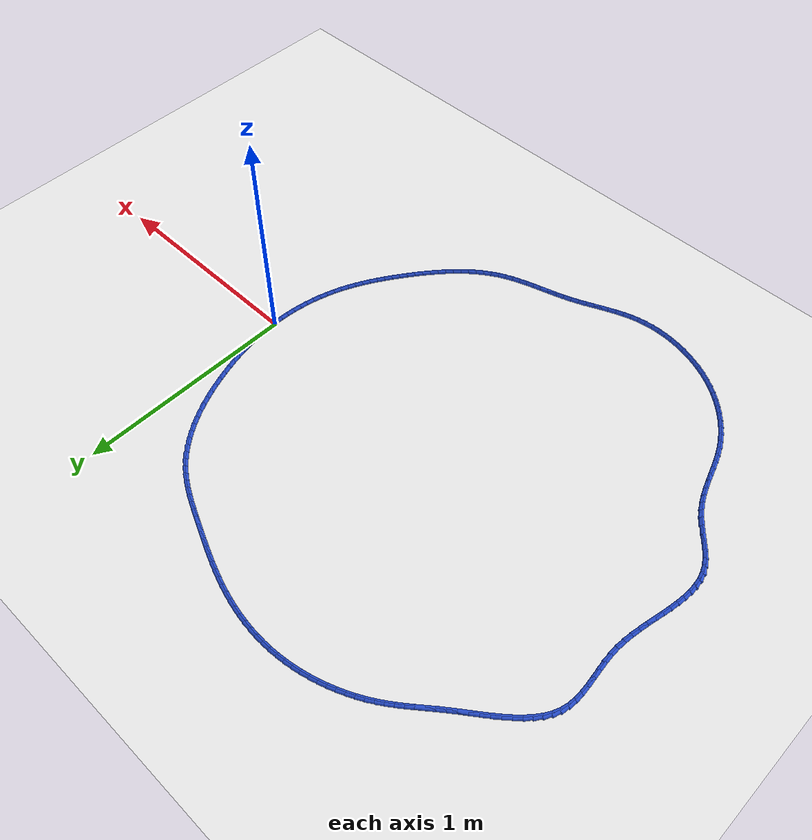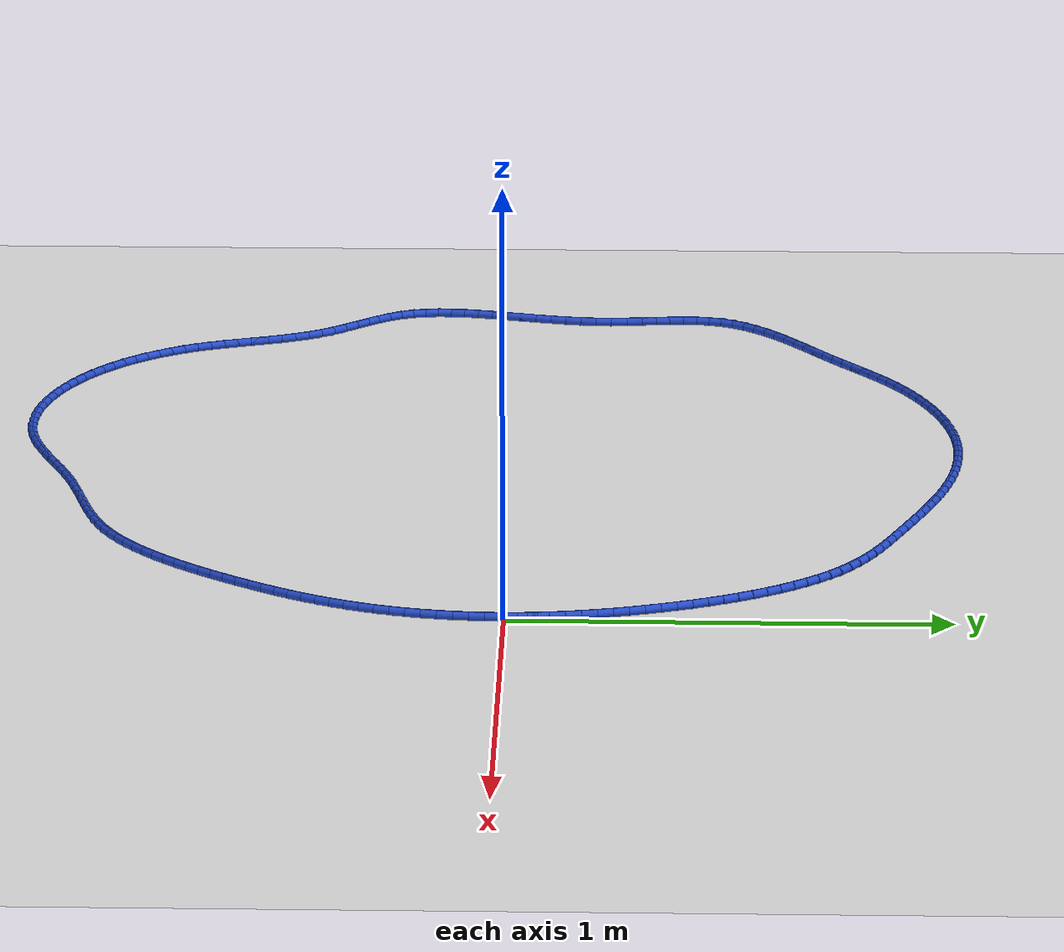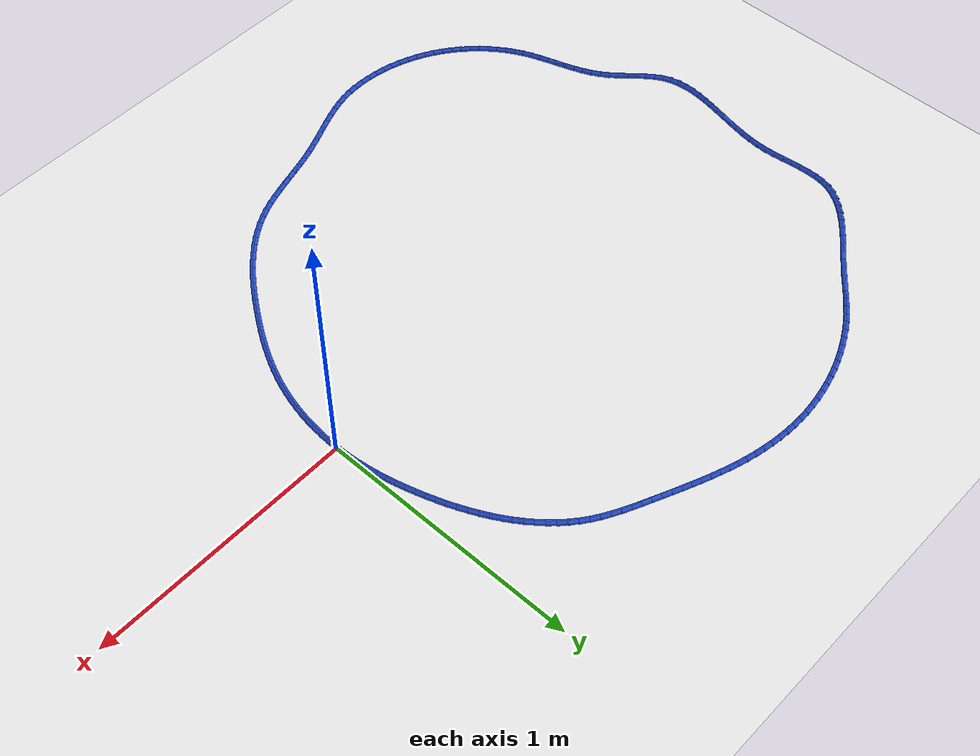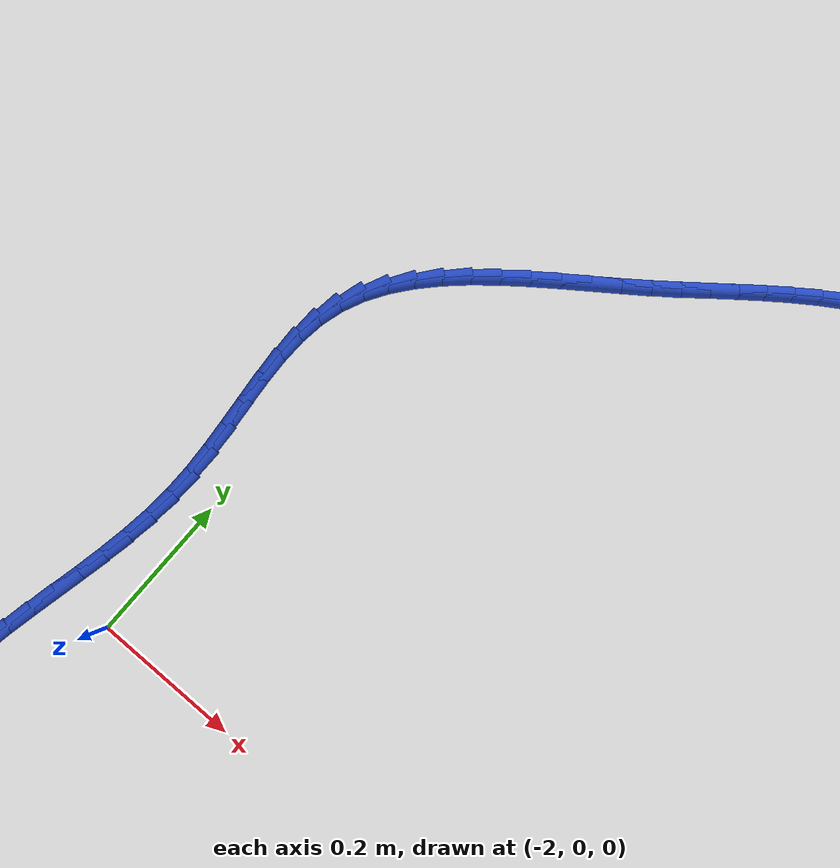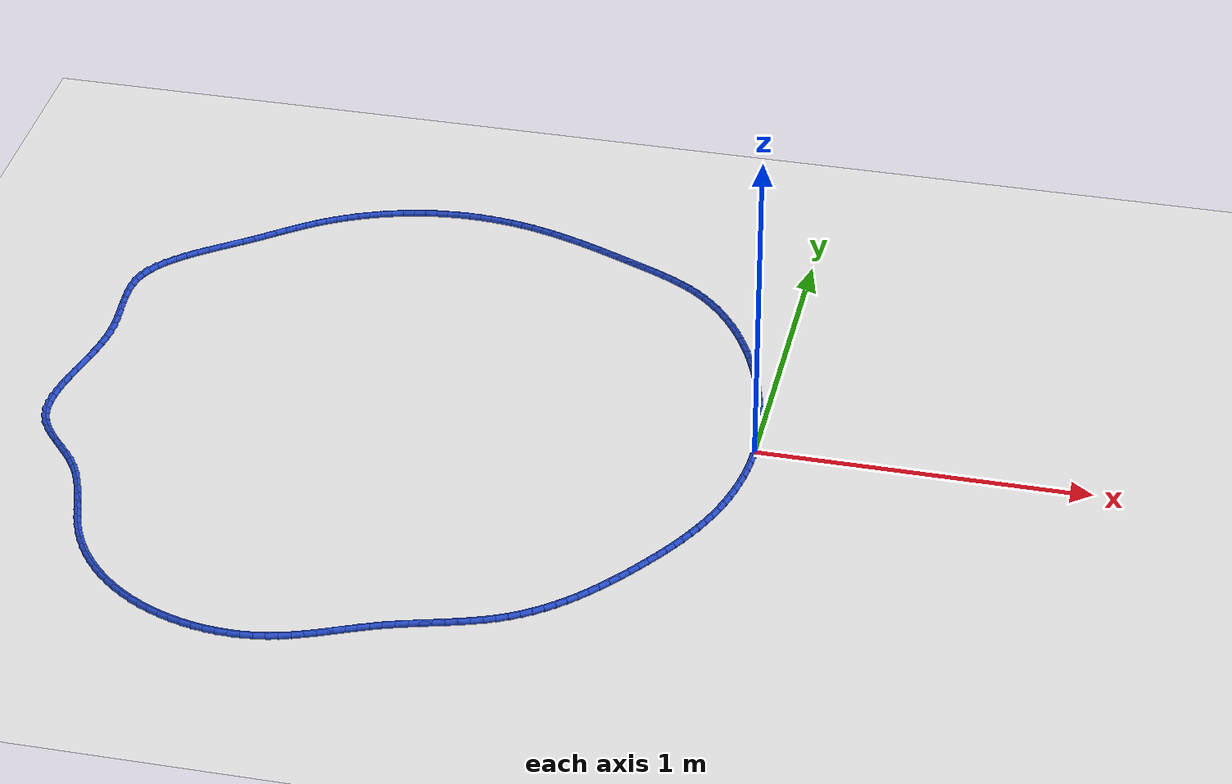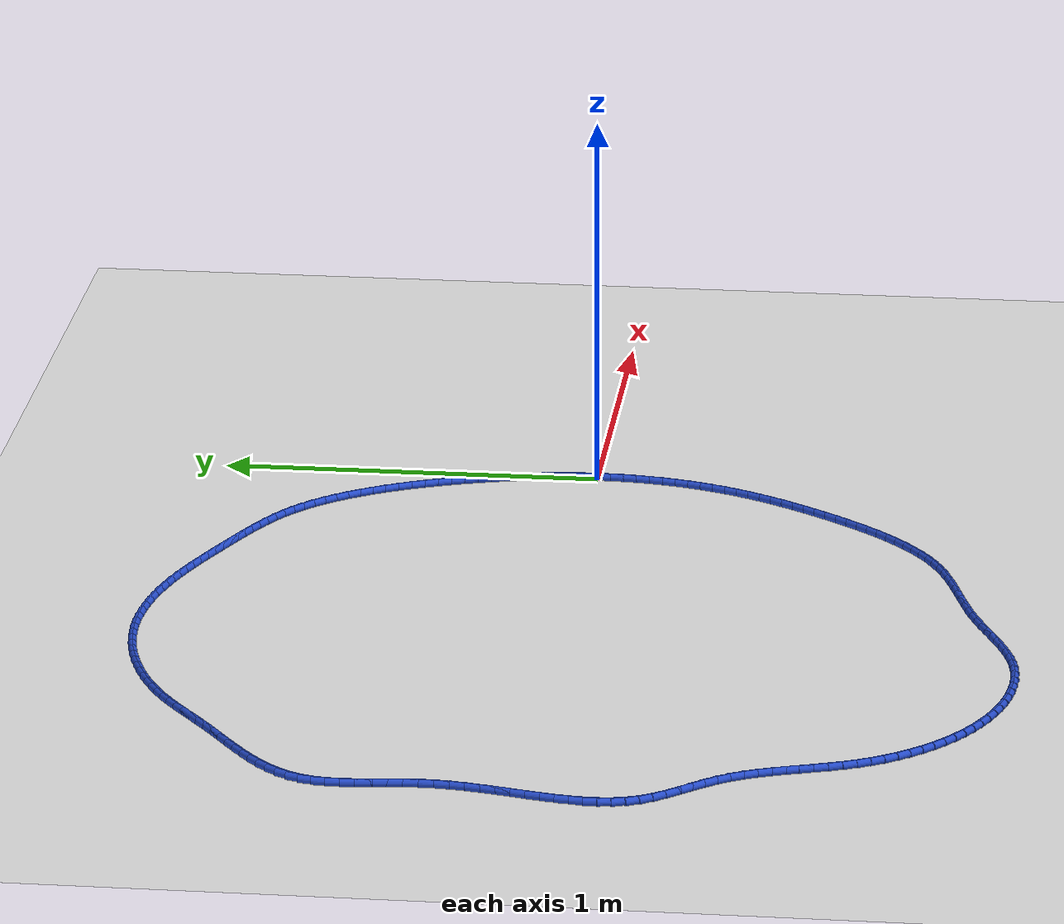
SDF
<sdf version="1.6">
 <world name="default">
  <light name="sun" type="directional">
   <pose>0 0 10 0 -0 0</pose>
   <diffuse>0.8 0.8 0.8 1</diffuse>
   <specular>0.2 0.2 0.2 1</specular>
   <attenuation>
    <range>1000</range>
    <constant>0.9</constant>
    <linear>0.01</linear>
    <quadratic>0.001</quadratic>
   </attenuation>
   <direction>-0.5 0.1 -0.9</direction>
  </light>
  <model name="ground_plane">
   <static>1</static>
   <link name="link">
    <collision name="collision">
     <geometry><plane><normal>0 0 1</normal><size>100 100</size></plane></geometry>
     <surface><friction><ode><mu>100</mu><mu2>50</mu2></ode></friction></surface>
    </collision>
    <visual name="visual">
     <cast_shadows>0</cast_shadows>
     <geometry><plane><normal>0 0 1</normal><size>100 100</size></plane></geometry>
     <material>
      <script><uri>file://media/materials/scripts/gazebo.material</uri><name>Gazebo/WhiteGlow</name></script>
     </material>
    </visual>
   </link>
  </model>
  <gravity>0 0 -9.8</gravity>
  <magnetic_field>6e-06 2.3e-05 -4.2e-05</magnetic_field>
  <atmosphere type="adiabatic"/>
  <physics name="default_physics" default="0" type="ode">
   <max_step_size>0.001</max_step_size>
   <real_time_factor>1</real_time_factor>
   <real_time_update_rate>1000</real_time_update_rate>
  </physics>
  <scene><ambient>0.4 0.4 0.4 1</ambient><background>0.7 0.7 0.7 1</background><shadows>1</shadows></scene>
  <spherical_coordinates>
   <surface_model>EARTH_WGS84</surface_model>
   <latitude_deg>0</latitude_deg>
   <longitude_deg>0</longitude_deg>
   <elevation>0</elevation>
   <heading_deg>0</heading_deg>
  </spherical_coordinates>
  <model name="line">
   <link name="link_0">
    <pose>1.214306433183765e-17 3.469446951953614e-17 0.01 0 1.57 -1.5426312727990603</pose>
    <collision name="collision">
     <geometry><cylinder><radius>0.01</radius><length>0.08</length></cylinder></geometry>
    </collision>
    <visual name="visual">
     <material>
      <script><name>Gazebo/Blue</name><uri>file://media/materials/scripts/gazebo.material</uri></script>
     </material>
     <geometry><cylinder><radius>0.01</radius><length>0.08</length></cylinder></geometry>
    </visual>
   </link>
   <link name="link_1">
    <pose>-0.0010002982026850779 0.035506187439576106 0.01 0 1.57 -1.5058562536619777</pose>
    <collision name="collision">
     <geometry><cylinder><radius>0.01</radius><length>0.08</length></cylinder></geometry>
    </collision>
    <visual name="visual">
     <material>
      <script><name>Gazebo/Blue</name><uri>file://media/materials/scripts/gazebo.material</uri></script>
     </material>
     <geometry><cylinder><radius>0.01</radius><length>0.08</length></cylinder></geometry>
    </visual>
   </link>
   <link name="link_2">
    <pose>-0.003300335182568896 0.07087422309153318 0.01 0 1.57 -1.4704358552611085</pose>
    <collision name="collision">
     <geometry><cylinder><radius>0.01</radius><length>0.08</length></cylinder></geometry>
    </collision>
    <visual name="visual">
     <material>
      <script><name>Gazebo/Blue</name><uri>file://media/materials/scripts/gazebo.material</uri></script>
     </material>
     <geometry><cylinder><radius>0.01</radius><length>0.08</length></cylinder></geometry>
    </visual>
   </link>
   <link name="link_3">
    <pose>-0.0068496619563330734 0.10612119006853507 0.01 0 1.57 -1.4364995870201744</pose>
    <collision name="collision">
     <geometry><cylinder><radius>0.01</radius><length>0.08</length></cylinder></geometry>
    </collision>
    <visual name="visual">
     <material>
      <script><name>Gazebo/Blue</name><uri>file://media/materials/scripts/gazebo.material</uri></script>
     </material>
     <geometry><cylinder><radius>0.01</radius><length>0.08</length></cylinder></geometry>
    </visual>
   </link>
   <link name="link_4">
    <pose>-0.01159782954065923 0.1412641714832455 0.01 0 1.57 -1.4041526083188234</pose>
    <collision name="collision">
     <geometry><cylinder><radius>0.01</radius><length>0.08</length></cylinder></geometry>
    </collision>
    <visual name="visual">
     <material>
      <script><name>Gazebo/Blue</name><uri>file://media/materials/scripts/gazebo.material</uri></script>
     </material>
     <geometry><cylinder><radius>0.01</radius><length>0.08</length></cylinder></geometry>
    </visual>
   </link>
   <link name="link_5">
    <pose>-0.017494388952228983 0.1763202504483281 0.01 0 1.57 -1.3734763381426565</pose>
    <collision name="collision">
     <geometry><cylinder><radius>0.01</radius><length>0.08</length></cylinder></geometry>
    </collision>
    <visual name="visual">
     <material>
      <script><name>Gazebo/Blue</name><uri>file://media/materials/scripts/gazebo.material</uri></script>
     </material>
     <geometry><cylinder><radius>0.01</radius><length>0.08</length></cylinder></geometry>
    </visual>
   </link>
   <link name="link_6">
    <pose>-0.024488891207723962 0.21130651007644682 0.01 0 1.57 -1.3445298664040357</pose>
    <collision name="collision">
     <geometry><cylinder><radius>0.01</radius><length>0.08</length></cylinder></geometry>
    </collision>
    <visual name="visual">
     <material>
      <script><name>Gazebo/Blue</name><uri>file://media/materials/scripts/gazebo.material</uri></script>
     </material>
     <geometry><cylinder><radius>0.01</radius><length>0.08</length></cylinder></geometry>
    </visual>
   </link>
   <link name="link_7">
    <pose>-0.032530887323825766 0.24624003348026519 0.01 0 1.57 -1.317351948800071</pose>
    <collision name="collision">
     <geometry><cylinder><radius>0.01</radius><length>0.08</length></cylinder></geometry>
    </collision>
    <visual name="visual">
     <material>
      <script><name>Gazebo/Blue</name><uri>file://media/materials/scripts/gazebo.material</uri></script>
     </material>
     <geometry><cylinder><radius>0.01</radius><length>0.08</length></cylinder></geometry>
    </visual>
   </link>
   <link name="link_8">
    <pose>-0.041569928317216044 0.2811379037724471 0.01 0 1.57 -1.2919633715170835</pose>
    <collision name="collision">
     <geometry><cylinder><radius>0.01</radius><length>0.08</length></cylinder></geometry>
    </collision>
    <visual name="visual">
     <material>
      <script><name>Gazebo/Blue</name><uri>file://media/materials/scripts/gazebo.material</uri></script>
     </material>
     <geometry><cylinder><radius>0.01</radius><length>0.08</length></cylinder></geometry>
    </visual>
   </link>
   <link name="link_9">
    <pose>-0.05155556520457641 0.31601720406565614 0.01 0 1.57 -1.2681315267713331</pose>
    <collision name="collision">
     <geometry><cylinder><radius>0.01</radius><length>0.08</length></cylinder></geometry>
    </collision>
    <visual name="visual">
     <material>
      <script><name>Gazebo/Blue</name><uri>file://media/materials/scripts/gazebo.material</uri></script>
     </material>
     <geometry><cylinder><radius>0.01</radius><length>0.08</length></cylinder></geometry>
    </visual>
   </link>
   <link name="link_10">
    <pose>-0.062443418650945125 0.35088528592256063 0.01 0 1.57 -1.2437487347819112</pose>
    <collision name="collision">
     <geometry><cylinder><radius>0.01</radius><length>0.08</length></cylinder></geometry>
    </collision>
    <visual name="visual">
     <material>
      <script><name>Gazebo/Blue</name><uri>file://media/materials/scripts/gazebo.material</uri></script>
     </material>
     <geometry><cylinder><radius>0.01</radius><length>0.08</length></cylinder></geometry>
    </visual>
   </link>
   <link name="link_11">
    <pose>-0.0742417528872694 0.38566509675859034 0.01 0 1.57 -1.2176183428503358</pose>
    <collision name="collision">
     <geometry><cylinder><radius>0.01</radius><length>0.08</length></cylinder></geometry>
    </collision>
    <visual name="visual">
     <material>
      <script><name>Gazebo/Blue</name><uri>file://media/materials/scripts/gazebo.material</uri></script>
     </material>
     <geometry><cylinder><radius>0.01</radius><length>0.08</length></cylinder></geometry>
    </visual>
   </link>
   <link name="link_12">
    <pose>-0.08698585982305533 0.42023625014350546 0.01 0 1.57 -1.1895678462801231</pose>
    <collision name="collision">
     <geometry><cylinder><radius>0.01</radius><length>0.08</length></cylinder></geometry>
    </collision>
    <visual name="visual">
     <material>
      <script><name>Gazebo/Blue</name><uri>file://media/materials/scripts/gazebo.material</uri></script>
     </material>
     <geometry><cylinder><radius>0.01</radius><length>0.08</length></cylinder></geometry>
    </visual>
   </link>
   <link name="link_13">
    <pose>-0.10071125241512836 0.45447800523888404 0.01 0 1.57 -1.1594206614155342</pose>
    <collision name="collision">
     <geometry><cylinder><radius>0.01</radius><length>0.08</length></cylinder></geometry>
    </collision>
    <visual name="visual">
     <material>
      <script><name>Gazebo/Blue</name><uri>file://media/materials/scripts/gazebo.material</uri></script>
     </material>
     <geometry><cylinder><radius>0.01</radius><length>0.08</length></cylinder></geometry>
    </visual>
   </link>
   <link name="link_14">
    <pose>-0.11545344362031383 0.4882696212063039 0.01 0 1.57 -1.1269881659741003</pose>
    <collision name="collision">
     <geometry><cylinder><radius>0.01</radius><length>0.08</length></cylinder></geometry>
    </collision>
    <visual name="visual">
     <material>
      <script><name>Gazebo/Blue</name><uri>file://media/materials/scripts/gazebo.material</uri></script>
     </material>
     <geometry><cylinder><radius>0.01</radius><length>0.08</length></cylinder></geometry>
    </visual>
   </link>
   <link name="link_15">
    <pose>-0.13124794639543733 0.5214903572073435 0.01 0 1.57 -1.0920713761530896</pose>
    <collision name="collision">
     <geometry><cylinder><radius>0.01</radius><length>0.08</length></cylinder></geometry>
    </collision>
    <visual name="visual">
     <material>
      <script><name>Gazebo/Blue</name><uri>file://media/materials/scripts/gazebo.material</uri></script>
     </material>
     <geometry><cylinder><radius>0.01</radius><length>0.08</length></cylinder></geometry>
    </visual>
   </link>
   <link name="link_16">
    <pose>-0.14813027369732415 0.5540194724035806 0.01 0 1.57 -1.054463975015782</pose>
    <collision name="collision">
     <geometry><cylinder><radius>0.01</radius><length>0.08</length></cylinder></geometry>
    </collision>
    <visual name="visual">
     <material>
      <script><name>Gazebo/Blue</name><uri>file://media/materials/scripts/gazebo.material</uri></script>
     </material>
     <geometry><cylinder><radius>0.01</radius><length>0.08</length></cylinder></geometry>
    </visual>
   </link>
   <link name="link_17">
    <pose>-0.16613593848279976 0.5857362259565936 0.01 0 1.57 -1.0139571616648602</pose>
    <collision name="collision">
     <geometry><cylinder><radius>0.01</radius><length>0.08</length></cylinder></geometry>
    </collision>
    <visual name="visual">
     <material>
      <script><name>Gazebo/Blue</name><uri>file://media/materials/scripts/gazebo.material</uri></script>
     </material>
     <geometry><cylinder><radius>0.01</radius><length>0.08</length></cylinder></geometry>
    </visual>
   </link>
   <link name="link_18">
    <pose>-0.18530045370868964 0.6165198770279604 0.01 0 1.57 -0.9703468603841444</pose>
    <collision name="collision">
     <geometry><cylinder><radius>0.01</radius><length>0.08</length></cylinder></geometry>
    </collision>
    <visual name="visual">
     <material>
      <script><name>Gazebo/Blue</name><uri>file://media/materials/scripts/gazebo.material</uri></script>
     </material>
     <geometry><cylinder><radius>0.01</radius><length>0.08</length></cylinder></geometry>
    </visual>
   </link>
   <link name="link_19">
    <pose>-0.20565933233181904 0.6462496847792587 0.01 0 1.57 -0.9234438483019581</pose>
    <collision name="collision">
     <geometry><cylinder><radius>0.01</radius><length>0.08</length></cylinder></geometry>
    </collision>
    <visual name="visual">
     <material>
      <script><name>Gazebo/Blue</name><uri>file://media/materials/scripts/gazebo.material</uri></script>
     </material>
     <geometry><cylinder><radius>0.01</radius><length>0.08</length></cylinder></geometry>
    </visual>
   </link>
   <link name="link_20">
    <pose>-0.2272480873090137 0.6748049083720674 0.01 0 1.57 -0.8730872771569701</pose>
    <collision name="collision">
     <geometry><cylinder><radius>0.01</radius><length>0.08</length></cylinder></geometry>
    </collision>
    <visual name="visual">
     <material>
      <script><name>Gazebo/Blue</name><uri>file://media/materials/scripts/gazebo.material</uri></script>
     </material>
     <geometry><cylinder><radius>0.01</radius><length>0.08</length></cylinder></geometry>
    </visual>
   </link>
   <link name="link_21">
    <pose>-0.25010223159709877 0.7020648069679638 0.01 0 1.57 -0.8191618086923206</pose>
    <collision name="collision">
     <geometry><cylinder><radius>0.01</radius><length>0.08</length></cylinder></geometry>
    </collision>
    <visual name="visual">
     <material>
      <script><name>Gazebo/Blue</name><uri>file://media/materials/scripts/gazebo.material</uri></script>
     </material>
     <geometry><cylinder><radius>0.01</radius><length>0.08</length></cylinder></geometry>
    </visual>
   </link>
   <link name="link_22">
    <pose>-0.27425727815289974 0.7279086397285263 0.01 0 1.57 -0.7616180754341912</pose>
    <collision name="collision">
     <geometry><cylinder><radius>0.01</radius><length>0.08</length></cylinder></geometry>
    </collision>
    <visual name="visual">
     <material>
      <script><name>Gazebo/Blue</name><uri>file://media/materials/scripts/gazebo.material</uri></script>
     </material>
     <geometry><cylinder><radius>0.01</radius><length>0.08</length></cylinder></geometry>
    </visual>
   </link>
   <link name="link_23">
    <pose>-0.29974873993324214 0.7522156658153332 0.01 0 1.57 -0.7004953626579496</pose>
    <collision name="collision">
     <geometry><cylinder><radius>0.01</radius><length>0.08</length></cylinder></geometry>
    </collision>
    <visual name="visual">
     <material>
      <script><name>Gazebo/Blue</name><uri>file://media/materials/scripts/gazebo.material</uri></script>
     </material>
     <geometry><cylinder><radius>0.01</radius><length>0.08</length></cylinder></geometry>
    </visual>
   </link>
   <link name="link_24">
    <pose>-0.32661212989495125 0.7748651443899621 0.01 0 1.57 -0.6363671307705628</pose>
    <collision name="collision">
     <geometry><cylinder><radius>0.01</radius><length>0.08</length></cylinder></geometry>
    </collision>
    <visual name="visual">
     <material>
      <script><name>Gazebo/Blue</name><uri>file://media/materials/scripts/gazebo.material</uri></script>
     </material>
     <geometry><cylinder><radius>0.01</radius><length>0.08</length></cylinder></geometry>
    </visual>
   </link>
   <link name="link_25">
    <pose>-0.35487483675196424 0.7957488059997493 0.01 0 1.57 -0.5762403225496664</pose>
    <collision name="collision">
     <geometry><cylinder><radius>0.01</radius><length>0.08</length></cylinder></geometry>
    </collision>
    <visual name="visual">
     <material>
      <script><name>Gazebo/Blue</name><uri>file://media/materials/scripts/gazebo.material</uri></script>
     </material>
     <geometry><cylinder><radius>0.01</radius><length>0.08</length></cylinder></geometry>
    </visual>
   </link>
   <link name="link_26">
    <pose>-0.3844347936793586 0.8149571061668767 0.01 0 1.57 -0.5257075585068931</pose>
    <collision name="collision">
     <geometry><cylinder><radius>0.01</radius><length>0.08</length></cylinder></geometry>
    </collision>
    <visual name="visual">
     <material>
      <script><name>Gazebo/Blue</name><uri>file://media/materials/scripts/gazebo.material</uri></script>
     </material>
     <geometry><cylinder><radius>0.01</radius><length>0.08</length></cylinder></geometry>
    </visual>
   </link>
   <link name="link_27">
    <pose>-0.4150860811227848 0.8327399229552338 0.01 0 1.57 -0.4848498554617234</pose>
    <collision name="collision">
     <geometry><cylinder><radius>0.01</radius><length>0.08</length></cylinder></geometry>
    </collision>
    <visual name="visual">
     <material>
      <script><name>Gazebo/Blue</name><uri>file://media/materials/scripts/gazebo.material</uri></script>
     </material>
     <geometry><cylinder><radius>0.01</radius><length>0.08</length></cylinder></geometry>
    </visual>
   </link>
   <link name="link_28">
    <pose>-0.44661985392086223 0.8493516254778275 0.01 0 1.57 -0.45344323892102056</pose>
    <collision name="collision">
     <geometry><cylinder><radius>0.01</radius><length>0.08</length></cylinder></geometry>
    </collision>
    <visual name="visual">
     <material>
      <script><name>Gazebo/Blue</name><uri>file://media/materials/scripts/gazebo.material</uri></script>
     </material>
     <geometry><cylinder><radius>0.01</radius><length>0.08</length></cylinder></geometry>
    </visual>
   </link>
   <link name="link_29">
    <pose>-0.4788272669122114 0.8650465828476643 0.01 0 1.57 -0.4312237591029039</pose>
    <collision name="collision">
     <geometry><cylinder><radius>0.01</radius><length>0.08</length></cylinder></geometry>
    </collision>
    <visual name="visual">
     <material>
      <script><name>Gazebo/Blue</name><uri>file://media/materials/scripts/gazebo.material</uri></script>
     </material>
     <geometry><cylinder><radius>0.01</radius><length>0.08</length></cylinder></geometry>
    </visual>
   </link>
   <link name="link_30">
    <pose>-0.5114994749354514 0.8800791641777507 0.01 0 1.57 -0.41796658264414865</pose>
    <collision name="collision">
     <geometry><cylinder><radius>0.01</radius><length>0.08</length></cylinder></geometry>
    </collision>
    <visual name="visual">
     <material>
      <script><name>Gazebo/Blue</name><uri>file://media/materials/scripts/gazebo.material</uri></script>
     </material>
     <geometry><cylinder><radius>0.01</radius><length>0.08</length></cylinder></geometry>
    </visual>
   </link>
   <link name="link_31">
    <pose>-0.5444276328292027 0.8947037385810938 0.01 0 1.57 -0.4133006790574649</pose>
    <collision name="collision">
     <geometry><cylinder><radius>0.01</radius><length>0.08</length></cylinder></geometry>
    </collision>
    <visual name="visual">
     <material>
      <script><name>Gazebo/Blue</name><uri>file://media/materials/scripts/gazebo.material</uri></script>
     </material>
     <geometry><cylinder><radius>0.01</radius><length>0.08</length></cylinder></geometry>
    </visual>
   </link>
   <link name="link_32">
    <pose>-0.5774077480621539 0.9091675324811481 0.01 0 1.57 -0.4114791212161708</pose>
    <collision name="collision">
     <geometry><cylinder><radius>0.01</radius><length>0.08</length></cylinder></geometry>
    </collision>
    <visual name="visual">
     <material>
      <script><name>Gazebo/Blue</name><uri>file://media/materials/scripts/gazebo.material</uri></script>
     </material>
     <geometry><cylinder><radius>0.01</radius><length>0.08</length></cylinder></geometry>
    </visual>
   </link>
   <link name="link_33">
    <pose>-0.6103534007896161 0.9235447145598118 0.01 0 1.57 -0.40660992484934555</pose>
    <collision name="collision">
     <geometry><cylinder><radius>0.01</radius><length>0.08</length></cylinder></geometry>
    </collision>
    <visual name="visual">
     <material>
      <script><name>Gazebo/Blue</name><uri>file://media/materials/scripts/gazebo.material</uri></script>
     </material>
     <geometry><cylinder><radius>0.01</radius><length>0.08</length></cylinder></geometry>
    </visual>
   </link>
   <link name="link_34">
    <pose>-0.6432991547878035 0.9377313751306118 0.01 0 1.57 -0.3984003694788667</pose>
    <collision name="collision">
     <geometry><cylinder><radius>0.01</radius><length>0.08</length></cylinder></geometry>
    </collision>
    <visual name="visual">
     <material>
      <script><name>Gazebo/Blue</name><uri>file://media/materials/scripts/gazebo.material</uri></script>
     </material>
     <geometry><cylinder><radius>0.01</radius><length>0.08</length></cylinder></geometry>
    </visual>
   </link>
   <link name="link_35">
    <pose>-0.6762851088247632 0.9516154574347079 0.01 0 1.57 -0.3868241258016433</pose>
    <collision name="collision">
     <geometry><cylinder><radius>0.01</radius><length>0.08</length></cylinder></geometry>
    </collision>
    <visual name="visual">
     <material>
      <script><name>Gazebo/Blue</name><uri>file://media/materials/scripts/gazebo.material</uri></script>
     </material>
     <geometry><cylinder><radius>0.01</radius><length>0.08</length></cylinder></geometry>
    </visual>
   </link>
   <link name="link_36">
    <pose>-0.7093513616685428 0.9650849047132605 0.01 0 1.57 -0.3718550755544408</pose>
    <collision name="collision">
     <geometry><cylinder><radius>0.01</radius><length>0.08</length></cylinder></geometry>
    </collision>
    <visual name="visual">
     <material>
      <script><name>Gazebo/Blue</name><uri>file://media/materials/scripts/gazebo.material</uri></script>
     </material>
     <geometry><cylinder><radius>0.01</radius><length>0.08</length></cylinder></geometry>
    </visual>
   </link>
   <link name="link_37">
    <pose>-0.7425380120871896 0.97802766020743 0.01 0 1.57 -0.353471273261738</pose>
    <collision name="collision">
     <geometry><cylinder><radius>0.01</radius><length>0.08</length></cylinder></geometry>
    </collision>
    <visual name="visual">
     <material>
      <script><name>Gazebo/Blue</name><uri>file://media/materials/scripts/gazebo.material</uri></script>
     </material>
     <geometry><cylinder><radius>0.01</radius><length>0.08</length></cylinder></geometry>
    </visual>
   </link>
   <link name="link_38">
    <pose>-0.775885158848751 0.9903316671583764 0.01 0 1.57 -0.3316601986304441</pose>
    <collision name="collision">
     <geometry><cylinder><radius>0.01</radius><length>0.08</length></cylinder></geometry>
    </collision>
    <visual name="visual">
     <material>
      <script><name>Gazebo/Blue</name><uri>file://media/materials/scripts/gazebo.material</uri></script>
     </material>
     <geometry><cylinder><radius>0.01</radius><length>0.08</length></cylinder></geometry>
    </visual>
   </link>
   <link name="link_39">
    <pose>-0.8094329007212744 1.0018848688072595 0.01 0 1.57 -0.30642528895157006</pose>
    <collision name="collision">
     <geometry><cylinder><radius>0.01</radius><length>0.08</length></cylinder></geometry>
    </collision>
    <visual name="visual">
     <material>
      <script><name>Gazebo/Blue</name><uri>file://media/materials/scripts/gazebo.material</uri></script>
     </material>
     <geometry><cylinder><radius>0.01</radius><length>0.08</length></cylinder></geometry>
    </visual>
   </link>
   <link name="link_40">
    <pose>-0.8432213364728072 1.01257520839524 0.01 0 1.57 -0.27779363498339904</pose>
    <collision name="collision">
     <geometry><cylinder><radius>0.01</radius><length>0.08</length></cylinder></geometry>
    </collision>
    <visual name="visual">
     <material>
      <script><name>Gazebo/Blue</name><uri>file://media/materials/scripts/gazebo.material</uri></script>
     </material>
     <geometry><cylinder><radius>0.01</radius><length>0.08</length></cylinder></geometry>
    </visual>
   </link>
   <link name="link_41">
    <pose>-0.8772905648713969 1.0222906291634777 0.01 0 1.57 -0.2458245611108107</pose>
    <collision name="collision">
     <geometry><cylinder><radius>0.01</radius><length>0.08</length></cylinder></geometry>
    </collision>
    <visual name="visual">
     <material>
      <script><name>Gazebo/Blue</name><uri>file://media/materials/scripts/gazebo.material</uri></script>
     </material>
     <geometry><cylinder><radius>0.01</radius><length>0.08</length></cylinder></geometry>
    </visual>
   </link>
   <link name="link_42">
    <pose>-0.911680684684798 1.0309190743533172 0.01 0 1.57 -0.2109621488366845</pose>
    <collision name="collision">
     <geometry><cylinder><radius>0.01</radius><length>0.08</length></cylinder></geometry>
    </collision>
    <visual name="visual">
     <material>
      <script><name>Gazebo/Blue</name><uri>file://media/materials/scripts/gazebo.material</uri></script>
     </material>
     <geometry><cylinder><radius>0.01</radius><length>0.08</length></cylinder></geometry>
    </visual>
   </link>
   <link name="link_43">
    <pose>-0.9464169433308423 1.038357792384751 0.01 0 1.57 -0.17461936030097</pose>
    <collision name="collision">
     <geometry><cylinder><radius>0.01</radius><length>0.08</length></cylinder></geometry>
    </collision>
    <visual name="visual">
     <material>
      <script><name>Gazebo/Blue</name><uri>file://media/materials/scripts/gazebo.material</uri></script>
     </material>
     <geometry><cylinder><radius>0.01</radius><length>0.08</length></cylinder></geometry>
    </visual>
   </link>
   <link name="link_44">
    <pose>-0.9814656636978952 1.0445409511010157 0.01 0 1.57 -0.13707113506609558</pose>
    <collision name="collision">
     <geometry><cylinder><radius>0.01</radius><length>0.08</length></cylinder></geometry>
    </collision>
    <visual name="visual">
     <material>
      <script><name>Gazebo/Blue</name><uri>file://media/materials/scripts/gazebo.material</uri></script>
     </material>
     <geometry><cylinder><radius>0.01</radius><length>0.08</length></cylinder></geometry>
    </visual>
   </link>
   <link name="link_45">
    <pose>-1.0167785567879724 1.0494118734870428 0.01 0 1.57 -0.09825086943430407</pose>
    <collision name="collision">
     <geometry><cylinder><radius>0.01</radius><length>0.08</length></cylinder></geometry>
    </collision>
    <visual name="visual">
     <material>
      <script><name>Gazebo/Blue</name><uri>file://media/materials/scripts/gazebo.material</uri></script>
     </material>
     <geometry><cylinder><radius>0.01</radius><length>0.08</length></cylinder></geometry>
    </visual>
   </link>
   <link name="link_46">
    <pose>-1.0523073336030901 1.052913882527763 0.01 0 1.57 -0.058103426087438105</pose>
    <collision name="collision">
     <geometry><cylinder><radius>0.01</radius><length>0.08</length></cylinder></geometry>
    </collision>
    <visual name="visual">
     <material>
      <script><name>Gazebo/Blue</name><uri>file://media/materials/scripts/gazebo.material</uri></script>
     </material>
     <geometry><cylinder><radius>0.01</radius><length>0.08</length></cylinder></geometry>
    </visual>
   </link>
   <link name="link_47">
    <pose>-1.088003705145264 1.0549903012081074 0.01 0 1.57 -0.01658761904739954</pose>
    <collision name="collision">
     <geometry><cylinder><radius>0.01</radius><length>0.08</length></cylinder></geometry>
    </collision>
    <visual name="visual">
     <material>
      <script><name>Gazebo/Blue</name><uri>file://media/materials/scripts/gazebo.material</uri></script>
     </material>
     <geometry><cylinder><radius>0.01</radius><length>0.08</length></cylinder></geometry>
    </visual>
   </link>
   <link name="link_48">
    <pose>-1.12381938241651 1.0555844525130071 0.01 0 1.57 0.026321033981479294</pose>
    <collision name="collision">
     <geometry><cylinder><radius>0.01</radius><length>0.08</length></cylinder></geometry>
    </collision>
    <visual name="visual">
     <material>
      <script><name>Gazebo/Blue</name><uri>file://media/materials/scripts/gazebo.material</uri></script>
     </material>
     <geometry><cylinder><radius>0.01</radius><length>0.08</length></cylinder></geometry>
    </visual>
   </link>
   <link name="link_49">
    <pose>-1.1597060764188438 1.0546396594273928 0.01 0 1.57 0.07058931030791428</pose>
    <collision name="collision">
     <geometry><cylinder><radius>0.01</radius><length>0.08</length></cylinder></geometry>
    </collision>
    <visual name="visual">
     <material>
      <script><name>Gazebo/Blue</name><uri>file://media/materials/scripts/gazebo.material</uri></script>
     </material>
     <geometry><cylinder><radius>0.01</radius><length>0.08</length></cylinder></geometry>
    </visual>
   </link>
   <link name="link_50">
    <pose>-1.1956148668783098 1.0521006641284496 0.01 0 1.57 0.11508070059896267</pose>
    <collision name="collision">
     <geometry><cylinder><radius>0.01</radius><length>0.08</length></cylinder></geometry>
    </collision>
    <visual name="visual">
     <material>
      <script><name>Gazebo/Blue</name><uri>file://media/materials/scripts/gazebo.material</uri></script>
     </material>
     <geometry><cylinder><radius>0.01</radius><length>0.08</length></cylinder></geometry>
    </visual>
   </link>
   <link name="link_51">
    <pose>-1.2314776979473683 1.0479552281050897 0.01 0 1.57 0.15860398806833617</pose>
    <collision name="collision">
     <geometry><cylinder><radius>0.01</radius><length>0.08</length></cylinder></geometry>
    </collision>
    <visual name="visual">
     <material>
      <script><name>Gazebo/Blue</name><uri>file://media/materials/scripts/gazebo.material</uri></script>
     </material>
     <geometry><cylinder><radius>0.01</radius><length>0.08</length></cylinder></geometry>
    </visual>
   </link>
   <link name="link_52">
    <pose>-1.2672043966700015 1.0422408350445127 0.01 0 1.57 0.2012730517212944</pose>
    <collision name="collision">
     <geometry><cylinder><radius>0.01</radius><length>0.08</length></cylinder></geometry>
    </collision>
    <visual name="visual">
     <material>
      <script><name>Gazebo/Blue</name><uri>file://media/materials/scripts/gazebo.material</uri></script>
     </material>
     <geometry><cylinder><radius>0.01</radius><length>0.08</length></cylinder></geometry>
    </visual>
   </link>
   <link name="link_53">
    <pose>-1.3027035585850202 1.034997737221158 0.01 0 1.57 0.24327899755496027</pose>
    <collision name="collision">
     <geometry><cylinder><radius>0.01</radius><length>0.08</length></cylinder></geometry>
    </collision>
    <visual name="visual">
     <material>
      <script><name>Gazebo/Blue</name><uri>file://media/materials/scripts/gazebo.material</uri></script>
     </material>
     <geometry><cylinder><radius>0.01</radius><length>0.08</length></cylinder></geometry>
    </visual>
   </link>
   <link name="link_54">
    <pose>-1.337883779231237 1.026266186909464 0.01 0 1.57 0.2848152551529933</pose>
    <collision name="collision">
     <geometry><cylinder><radius>0.01</radius><length>0.08</length></cylinder></geometry>
    </collision>
    <visual name="visual">
     <material>
      <script><name>Gazebo/Blue</name><uri>file://media/materials/scripts/gazebo.material</uri></script>
     </material>
     <geometry><cylinder><radius>0.01</radius><length>0.08</length></cylinder></geometry>
    </visual>
   </link>
   <link name="link_55">
    <pose>-1.372653654147463 1.0160864363838709 0.01 0 1.57 0.3260774939272924</pose>
    <collision name="collision">
     <geometry><cylinder><radius>0.01</radius><length>0.08</length></cylinder></geometry>
    </collision>
    <visual name="visual">
     <material>
      <script><name>Gazebo/Blue</name><uri>file://media/materials/scripts/gazebo.material</uri></script>
     </material>
     <geometry><cylinder><radius>0.01</radius><length>0.08</length></cylinder></geometry>
    </visual>
   </link>
   <link name="link_56">
    <pose>-1.4069217788725088 1.0044987379188164 0.01 0 1.57 0.36726392074485914</pose>
    <collision name="collision">
     <geometry><cylinder><radius>0.01</radius><length>0.08</length></cylinder></geometry>
    </collision>
    <visual name="visual">
     <material>
      <script><name>Gazebo/Blue</name><uri>file://media/materials/scripts/gazebo.material</uri></script>
     </material>
     <geometry><cylinder><radius>0.01</radius><length>0.08</length></cylinder></geometry>
    </visual>
   </link>
   <link name="link_57">
    <pose>-1.4405967489451879 0.9915433437887409 0.01 0 1.57 0.4085758394882021</pose>
    <collision name="collision">
     <geometry><cylinder><radius>0.01</radius><length>0.08</length></cylinder></geometry>
    </collision>
    <visual name="visual">
     <material>
      <script><name>Gazebo/Blue</name><uri>file://media/materials/scripts/gazebo.material</uri></script>
     </material>
     <geometry><cylinder><radius>0.01</radius><length>0.08</length></cylinder></geometry>
    </visual>
   </link>
   <link name="link_58">
    <pose>-1.4735871599043096 0.9772605062680824 0.01 0 1.57 0.4502183592385526</pose>
    <collision name="collision">
     <geometry><cylinder><radius>0.01</radius><length>0.08</length></cylinder></geometry>
    </collision>
    <visual name="visual">
     <material>
      <script><name>Gazebo/Blue</name><uri>file://media/materials/scripts/gazebo.material</uri></script>
     </material>
     <geometry><cylinder><radius>0.01</radius><length>0.08</length></cylinder></geometry>
    </visual>
   </link>
   <link name="link_59">
    <pose>-1.5058016072886864 0.9616904776312803 0.01 0 1.57 0.4924011363726101</pose>
    <collision name="collision">
     <geometry><cylinder><radius>0.01</radius><length>0.08</length></cylinder></geometry>
    </collision>
    <visual name="visual">
     <material>
      <script><name>Gazebo/Blue</name><uri>file://media/materials/scripts/gazebo.material</uri></script>
     </material>
     <geometry><cylinder><radius>0.01</radius><length>0.08</length></cylinder></geometry>
    </visual>
   </link>
   <link name="link_60">
    <pose>-1.5371486866371304 0.9448735101527739 0.01 0 1.57 0.5353390253562064</pose>
    <collision name="collision">
     <geometry><cylinder><radius>0.01</radius><length>0.08</length></cylinder></geometry>
    </collision>
    <visual name="visual">
     <material>
      <script><name>Gazebo/Blue</name><uri>file://media/materials/scripts/gazebo.material</uri></script>
     </material>
     <geometry><cylinder><radius>0.01</radius><length>0.08</length></cylinder></geometry>
    </visual>
   </link>
   <link name="link_61">
    <pose>-1.5675369934884518 0.9268498561070015 0.01 0 1.57 0.5789739143311479</pose>
    <collision name="collision">
     <geometry><cylinder><radius>0.01</radius><length>0.08</length></cylinder></geometry>
    </collision>
    <visual name="visual">
     <material>
      <script><name>Gazebo/Blue</name><uri>file://media/materials/scripts/gazebo.material</uri></script>
     </material>
     <geometry><cylinder><radius>0.01</radius><length>0.08</length></cylinder></geometry>
    </visual>
   </link>
   <link name="link_62">
    <pose>-1.5968869336315832 0.9076637149754472 0.01 0 1.57 0.6182181899341216</pose>
    <collision name="collision">
     <geometry><cylinder><radius>0.01</radius><length>0.08</length></cylinder></geometry>
    </collision>
    <visual name="visual">
     <material>
      <script><name>Gazebo/Blue</name><uri>file://media/materials/scripts/gazebo.material</uri></script>
     </material>
     <geometry><cylinder><radius>0.01</radius><length>0.08</length></cylinder></geometry>
    </visual>
   </link>
   <link name="link_63">
    <pose>-1.6253343342150104 0.887431284097323 0.01 0 1.57 0.6480325184418043</pose>
    <collision name="collision">
     <geometry><cylinder><radius>0.01</radius><length>0.08</length></cylinder></geometry>
    </collision>
    <visual name="visual">
     <material>
      <script><name>Gazebo/Blue</name><uri>file://media/materials/scripts/gazebo.material</uri></script>
     </material>
     <geometry><cylinder><radius>0.01</radius><length>0.08</length></cylinder></geometry>
    </visual>
   </link>
   <link name="link_64">
    <pose>-1.653203187637707 0.8663316491668405 0.01 0 1.57 0.6678405271354885</pose>
    <collision name="collision">
     <geometry><cylinder><radius>0.01</radius><length>0.08</length></cylinder></geometry>
    </collision>
    <visual name="visual">
     <material>
      <script><name>Gazebo/Blue</name><uri>file://media/materials/scripts/gazebo.material</uri></script>
     </material>
     <geometry><cylinder><radius>0.01</radius><length>0.08</length></cylinder></geometry>
    </visual>
   </link>
   <link name="link_65">
    <pose>-1.6808238140370773 0.8445460107270466 0.01 0 1.57 0.6775577919312228</pose>
    <collision name="collision">
     <geometry><cylinder><radius>0.01</radius><length>0.08</length></cylinder></geometry>
    </collision>
    <visual name="visual">
     <material>
      <script><name>Gazebo/Blue</name><uri>file://media/materials/scripts/gazebo.material</uri></script>
     </material>
     <geometry><cylinder><radius>0.01</radius><length>0.08</length></cylinder></geometry>
    </visual>
   </link>
   <link name="link_66">
    <pose>-1.7085265335505269 0.8222555693209891 0.01 0 1.57 0.677379914728722</pose>
    <collision name="collision">
     <geometry><cylinder><radius>0.01</radius><length>0.08</length></cylinder></geometry>
    </collision>
    <visual name="visual">
     <material>
      <script><name>Gazebo/Blue</name><uri>file://media/materials/scripts/gazebo.material</uri></script>
     </material>
     <geometry><cylinder><radius>0.01</radius><length>0.08</length></cylinder></geometry>
    </visual>
   </link>
   <link name="link_67">
    <pose>-1.7366416663154605 0.7996415254917143 0.01 0 1.57 0.66773242908719</pose>
    <collision name="collision">
     <geometry><cylinder><radius>0.01</radius><length>0.08</length></cylinder></geometry>
    </collision>
    <visual name="visual">
     <material>
      <script><name>Gazebo/Blue</name><uri>file://media/materials/scripts/gazebo.material</uri></script>
     </material>
     <geometry><cylinder><radius>0.01</radius><length>0.08</length></cylinder></geometry>
    </visual>
   </link>
   <link name="link_68">
    <pose>-1.7654995324692837 0.7768850797822697 0.01 0 1.57 0.6503580091543768</pose>
    <collision name="collision">
     <geometry><cylinder><radius>0.01</radius><length>0.08</length></cylinder></geometry>
    </collision>
    <visual name="visual">
     <material>
      <script><name>Gazebo/Blue</name><uri>file://media/materials/scripts/gazebo.material</uri></script>
     </material>
     <geometry><cylinder><radius>0.01</radius><length>0.08</length></cylinder></geometry>
    </visual>
   </link>
   <link name="link_69">
    <pose>-1.7953840942951569 0.7541498178366893 0.01 0 1.57 0.6378620914643786</pose>
    <collision name="collision">
     <geometry><cylinder><radius>0.01</radius><length>0.08</length></cylinder></geometry>
    </collision>
    <visual name="visual">
     <material>
      <script><name>Gazebo/Blue</name><uri>file://media/materials/scripts/gazebo.material</uri></script>
     </material>
     <geometry><cylinder><radius>0.01</radius><length>0.08</length></cylinder></geometry>
    </visual>
   </link>
   <link name="link_70">
    <pose>-1.8260689540610617 0.7314054004447561 0.01 0 1.57 0.6372073438644877</pose>
    <collision name="collision">
     <geometry><cylinder><radius>0.01</radius><length>0.08</length></cylinder></geometry>
    </collision>
    <visual name="visual">
     <material>
      <script><name>Gazebo/Blue</name><uri>file://media/materials/scripts/gazebo.material</uri></script>
     </material>
     <geometry><cylinder><radius>0.01</radius><length>0.08</length></cylinder></geometry>
    </visual>
   </link>
   <link name="link_71">
    <pose>-1.8570115179811308 0.7085013413004101 0.01 0 1.57 0.6482083874129648</pose>
    <collision name="collision">
     <geometry><cylinder><radius>0.01</radius><length>0.08</length></cylinder></geometry>
    </collision>
    <visual name="visual">
     <material>
      <script><name>Gazebo/Blue</name><uri>file://media/materials/scripts/gazebo.material</uri></script>
     </material>
     <geometry><cylinder><radius>0.01</radius><length>0.08</length></cylinder></geometry>
    </visual>
   </link>
   <link name="link_72">
    <pose>-1.887664479541199 0.685285363371201 0.01 0 1.57 0.6711997814016368</pose>
    <collision name="collision">
     <geometry><cylinder><radius>0.01</radius><length>0.08</length></cylinder></geometry>
    </collision>
    <visual name="visual">
     <material>
      <script><name>Gazebo/Blue</name><uri>file://media/materials/scripts/gazebo.material</uri></script>
     </material>
     <geometry><cylinder><radius>0.01</radius><length>0.08</length></cylinder></geometry>
    </visual>
   </link>
   <link name="link_73">
    <pose>-1.9174805322271027 0.6616051896246796 0.01 0 1.57 0.7071341226492847</pose>
    <collision name="collision">
     <geometry><cylinder><radius>0.01</radius><length>0.08</length></cylinder></geometry>
    </collision>
    <visual name="visual">
     <material>
      <script><name>Gazebo/Blue</name><uri>file://media/materials/scripts/gazebo.material</uri></script>
     </material>
     <geometry><cylinder><radius>0.01</radius><length>0.08</length></cylinder></geometry>
    </visual>
   </link>
   <link name="link_74">
    <pose>-1.945912369524679 0.6373085430283953 0.01 0 1.57 0.7575783454623276</pose>
    <collision name="collision">
     <geometry><cylinder><radius>0.01</radius><length>0.08</length></cylinder></geometry>
    </collision>
    <visual name="visual">
     <material>
      <script><name>Gazebo/Blue</name><uri>file://media/materials/scripts/gazebo.material</uri></script>
     </material>
     <geometry><cylinder><radius>0.01</radius><length>0.08</length></cylinder></geometry>
    </visual>
   </link>
   <link name="link_75">
    <pose>-1.972412684919763 0.6122431465498984 0.01 0 1.57 0.82467047277986</pose>
    <collision name="collision">
     <geometry><cylinder><radius>0.01</radius><length>0.08</length></cylinder></geometry>
    </collision>
    <visual name="visual">
     <material>
      <script><name>Gazebo/Blue</name><uri>file://media/materials/scripts/gazebo.material</uri></script>
     </material>
     <geometry><cylinder><radius>0.01</radius><length>0.08</length></cylinder></geometry>
    </visual>
   </link>
   <link name="link_76">
    <pose>-1.9964341718981913 0.5862567231567393 0.01 0 1.57 0.9109309219383204</pose>
    <collision name="collision">
     <geometry><cylinder><radius>0.01</radius><length>0.08</length></cylinder></geometry>
    </collision>
    <visual name="visual">
     <material>
      <script><name>Gazebo/Blue</name><uri>file://media/materials/scripts/gazebo.material</uri></script>
     </material>
     <geometry><cylinder><radius>0.01</radius><length>0.08</length></cylinder></geometry>
    </visual>
   </link>
   <link name="link_77">
    <pose>-2.0174295239458004 0.5591969958164673 0.01 0 1.57 1.018742256249772</pose>
    <collision name="collision">
     <geometry><cylinder><radius>0.01</radius><length>0.08</length></cylinder></geometry>
    </collision>
    <visual name="visual">
     <material>
      <script><name>Gazebo/Blue</name><uri>file://media/materials/scripts/gazebo.material</uri></script>
     </material>
     <geometry><cylinder><radius>0.01</radius><length>0.08</length></cylinder></geometry>
    </visual>
   </link>
   <link name="link_78">
    <pose>-2.0348514345484268 0.5309116874966329 0.01 0 1.57 1.149268176694557</pose>
    <collision name="collision">
     <geometry><cylinder><radius>0.01</radius><length>0.08</length></cylinder></geometry>
    </collision>
    <visual name="visual">
     <material>
      <script><name>Gazebo/Blue</name><uri>file://media/materials/scripts/gazebo.material</uri></script>
     </material>
     <geometry><cylinder><radius>0.01</radius><length>0.08</length></cylinder></geometry>
    </visual>
   </link>
   <link name="link_79">
    <pose>-2.048152597191906 0.5012485211647859 0.01 0 1.57 1.2992589470026006</pose>
    <collision name="collision">
     <geometry><cylinder><radius>0.01</radius><length>0.08</length></cylinder></geometry>
    </collision>
    <visual name="visual">
     <material>
      <script><name>Gazebo/Blue</name><uri>file://media/materials/scripts/gazebo.material</uri></script>
     </material>
     <geometry><cylinder><radius>0.01</radius><length>0.08</length></cylinder></geometry>
    </visual>
   </link>
   <link name="link_80">
    <pose>-2.0568342234120514 0.4700660844668847 0.01 0 1.57 1.4384650399189565</pose>
    <collision name="collision">
     <geometry><cylinder><radius>0.01</radius><length>0.08</length></cylinder></geometry>
    </collision>
    <visual name="visual">
     <material>
      <script><name>Gazebo/Blue</name><uri>file://media/materials/scripts/gazebo.material</uri></script>
     </material>
     <geometry><cylinder><radius>0.01</radius><length>0.08</length></cylinder></geometry>
    </visual>
   </link>
   <link name="link_81">
    <pose>-2.0611825448047374 0.4373987551002222 0.01 0 1.57 1.543217004678586</pose>
    <collision name="collision">
     <geometry><cylinder><radius>0.01</radius><length>0.08</length></cylinder></geometry>
    </collision>
    <visual name="visual">
     <material>
      <script><name>Gazebo/Blue</name><uri>file://media/materials/scripts/gazebo.material</uri></script>
     </material>
     <geometry><cylinder><radius>0.01</radius><length>0.08</length></cylinder></geometry>
    </visual>
   </link>
   <link name="link_82">
    <pose>-2.0621198015702404 0.4034233325814914 0.01 0 1.57 -1.5271445264301924</pose>
    <collision name="collision">
     <geometry><cylinder><radius>0.01</radius><length>0.08</length></cylinder></geometry>
    </collision>
    <visual name="visual">
     <material>
      <script><name>Gazebo/Blue</name><uri>file://media/materials/scripts/gazebo.material</uri></script>
     </material>
     <geometry><cylinder><radius>0.01</radius><length>0.08</length></cylinder></geometry>
    </visual>
   </link>
   <link name="link_83">
    <pose>-2.060586535105886 0.3683207146263131 0.01 0 1.57 -1.4860252019360927</pose>
    <collision name="collision">
     <geometry><cylinder><radius>0.01</radius><length>0.08</length></cylinder></geometry>
    </collision>
    <visual name="visual">
     <material>
      <script><name>Gazebo/Blue</name><uri>file://media/materials/scripts/gazebo.material</uri></script>
     </material>
     <geometry><cylinder><radius>0.01</radius><length>0.08</length></cylinder></geometry>
    </visual>
   </link>
   <link name="link_84">
    <pose>-2.0575232868089994 0.33227179895030695 0.01 0 1.57 -1.4719007553009327</pose>
    <collision name="collision">
     <geometry><cylinder><radius>0.01</radius><length>0.08</length></cylinder></geometry>
    </collision>
    <visual name="visual">
     <material>
      <script><name>Gazebo/Blue</name><uri>file://media/materials/scripts/gazebo.material</uri></script>
     </material>
     <geometry><cylinder><radius>0.01</radius><length>0.08</length></cylinder></geometry>
    </visual>
   </link>
   <link name="link_85">
    <pose>-2.053870598076907 0.29545748326909405 0.01 0 1.57 -1.4827440591141536</pose>
    <collision name="collision">
     <geometry><cylinder><radius>0.01</radius><length>0.08</length></cylinder></geometry>
    </collision>
    <visual name="visual">
     <material>
      <script><name>Gazebo/Blue</name><uri>file://media/materials/scripts/gazebo.material</uri></script>
     </material>
     <geometry><cylinder><radius>0.01</radius><length>0.08</length></cylinder></geometry>
    </visual>
   </link>
   <link name="link_86">
    <pose>-2.0505690103069334 0.25805866529829513 0.01 0 1.57 -1.5176765945664916</pose>
    <collision name="collision">
     <geometry><cylinder><radius>0.01</radius><length>0.08</length></cylinder></geometry>
    </collision>
    <visual name="visual">
     <material>
      <script><name>Gazebo/Blue</name><uri>file://media/materials/scripts/gazebo.material</uri></script>
     </material>
     <geometry><cylinder><radius>0.01</radius><length>0.08</length></cylinder></geometry>
    </visual>
   </link>
   <link name="link_87">
    <pose>-2.0485590648964047 0.22025624275353 0.01 0 1.57 1.565137476093093</pose>
    <collision name="collision">
     <geometry><cylinder><radius>0.01</radius><length>0.08</length></cylinder></geometry>
    </collision>
    <visual name="visual">
     <material>
      <script><name>Gazebo/Blue</name><uri>file://media/materials/scripts/gazebo.material</uri></script>
     </material>
     <geometry><cylinder><radius>0.01</radius><length>0.08</length></cylinder></geometry>
    </visual>
   </link>
   <link name="link_88">
    <pose>-2.0487742480200803 0.18223070751629977 0.01 0 1.57 1.496114686961703</pose>
    <collision name="collision">
     <geometry><cylinder><radius>0.01</radius><length>0.08</length></cylinder></geometry>
    </collision>
    <visual name="visual">
     <material>
      <script><name>Gazebo/Blue</name><uri>file://media/materials/scripts/gazebo.material</uri></script>
     </material>
     <geometry><cylinder><radius>0.01</radius><length>0.08</length></cylinder></geometry>
    </visual>
   </link>
   <link name="link_89">
    <pose>-2.0516247896411275 0.14413245245675652 0.01 0 1.57 1.4396492433320283</pose>
    <collision name="collision">
     <geometry><cylinder><radius>0.01</radius><length>0.08</length></cylinder></geometry>
    </collision>
    <visual name="visual">
     <material>
      <script><name>Gazebo/Blue</name><uri>file://media/materials/scripts/gazebo.material</uri></script>
     </material>
     <geometry><cylinder><radius>0.01</radius><length>0.08</length></cylinder></geometry>
    </visual>
   </link>
   <link name="link_90">
    <pose>-2.0566464980952928 0.10606157151710112 0.01 0 1.57 1.3974329858172503</pose>
    <collision name="collision">
     <geometry><cylinder><radius>0.01</radius><length>0.08</length></cylinder></geometry>
    </collision>
    <visual name="visual">
     <material>
      <script><name>Gazebo/Blue</name><uri>file://media/materials/scripts/gazebo.material</uri></script>
     </material>
     <geometry><cylinder><radius>0.01</radius><length>0.08</length></cylinder></geometry>
    </visual>
   </link>
   <link name="link_91">
    <pose>-2.0632920347307357 0.06811337581599951 0.01 0 1.57 1.368919878590793</pose>
    <collision name="collision">
     <geometry><cylinder><radius>0.01</radius><length>0.08</length></cylinder></geometry>
    </collision>
    <visual name="visual">
     <material>
      <script><name>Gazebo/Blue</name><uri>file://media/materials/scripts/gazebo.material</uri></script>
     </material>
     <geometry><cylinder><radius>0.01</radius><length>0.08</length></cylinder></geometry>
    </visual>
   </link>
   <link name="link_92">
    <pose>-2.0710140608956173 0.030383176472118925 0.01 0 1.57 1.353749978917285</pose>
    <collision name="collision">
     <geometry><cylinder><radius>0.01</radius><length>0.08</length></cylinder></geometry>
    </collision>
    <visual name="visual">
     <material>
      <script><name>Gazebo/Blue</name><uri>file://media/materials/scripts/gazebo.material</uri></script>
     </material>
     <geometry><cylinder><radius>0.01</radius><length>0.08</length></cylinder></geometry>
    </visual>
   </link>
   <link name="link_93">
    <pose>-2.0792652379380963 -0.0070337153958735694 0.01 0 1.57 1.351897488018428</pose>
    <collision name="collision">
     <geometry><cylinder><radius>0.01</radius><length>0.08</length></cylinder></geometry>
    </collision>
    <visual name="visual">
     <material>
      <script><name>Gazebo/Blue</name><uri>file://media/materials/scripts/gazebo.material</uri></script>
     </material>
     <geometry><cylinder><radius>0.01</radius><length>0.08</length></cylinder></geometry>
    </visual>
   </link>
   <link name="link_94">
    <pose>-2.0874982272063334 -0.04404198866931199 0.01 0 1.57 1.3637634474271687</pose>
    <collision name="collision">
     <geometry><cylinder><radius>0.01</radius><length>0.08</length></cylinder></geometry>
    </collision>
    <visual name="visual">
     <material>
      <script><name>Gazebo/Blue</name><uri>file://media/materials/scripts/gazebo.material</uri></script>
     </material>
     <geometry><cylinder><radius>0.01</radius><length>0.08</length></cylinder></geometry>
    </visual>
   </link>
   <link name="link_95">
    <pose>-2.0951656900484874 -0.08054633222952923 0.01 0 1.57 1.3902312500006266</pose>
    <collision name="collision">
     <geometry><cylinder><radius>0.01</radius><length>0.08</length></cylinder></geometry>
    </collision>
    <visual name="visual">
     <material>
      <script><name>Gazebo/Blue</name><uri>file://media/materials/scripts/gazebo.material</uri></script>
     </material>
     <geometry><cylinder><radius>0.01</radius><length>0.08</length></cylinder></geometry>
    </visual>
   </link>
   <link name="link_96">
    <pose>-2.1017202878127192 -0.11645143495785845 0.01 0 1.57 1.4326777446845138</pose>
    <collision name="collision">
     <geometry><cylinder><radius>0.01</radius><length>0.08</length></cylinder></geometry>
    </collision>
    <visual name="visual">
     <material>
      <script><name>Gazebo/Blue</name><uri>file://media/materials/scripts/gazebo.material</uri></script>
     </material>
     <geometry><cylinder><radius>0.01</radius><length>0.08</length></cylinder></geometry>
    </visual>
   </link>
   <link name="link_97">
    <pose>-2.106614681847189 -0.15166198573563297 0.01 0 1.57 1.4928950852606986</pose>
    <collision name="collision">
     <geometry><cylinder><radius>0.01</radius><length>0.08</length></cylinder></geometry>
    </collision>
    <visual name="visual">
     <material>
      <script><name>Gazebo/Blue</name><uri>file://media/materials/scripts/gazebo.material</uri></script>
     </material>
     <geometry><cylinder><radius>0.01</radius><length>0.08</length></cylinder></geometry>
    </visual>
   </link>
   <link name="link_98">
    <pose>-2.109301533500055 -0.18608267344418533 0.01 0 1.57 -1.5687677523042094</pose>
    <collision name="collision">
     <geometry><cylinder><radius>0.01</radius><length>0.08</length></cylinder></geometry>
    </collision>
    <visual name="visual">
     <material>
      <script><name>Gazebo/Blue</name><uri>file://media/materials/scripts/gazebo.material</uri></script>
     </material>
     <geometry><cylinder><radius>0.01</radius><length>0.08</length></cylinder></geometry>
    </visual>
   </link>
   <link name="link_99">
    <pose>-2.1092335041194787 -0.21961818696485014 0.01 0 1.57 -1.4676391180090493</pose>
    <collision name="collision">
     <geometry><cylinder><radius>0.01</radius><length>0.08</length></cylinder></geometry>
    </collision>
    <visual name="visual">
     <material>
      <script><name>Gazebo/Blue</name><uri>file://media/materials/scripts/gazebo.material</uri></script>
     </material>
     <geometry><cylinder><radius>0.01</radius><length>0.08</length></cylinder></geometry>
    </visual>
   </link>
   <link name="link_100">
    <pose>-2.10586325505362 -0.2521732151789601 0.01 0 1.57 -1.3453439930193554</pose>
    <collision name="collision">
     <geometry><cylinder><radius>0.01</radius><length>0.08</length></cylinder></geometry>
    </collision>
    <visual name="visual">
     <material>
      <script><name>Gazebo/Blue</name><uri>file://media/materials/scripts/gazebo.material</uri></script>
     </material>
     <geometry><cylinder><radius>0.01</radius><length>0.08</length></cylinder></geometry>
    </visual>
   </link>
   <link name="link_101">
    <pose>-2.0986434476506375 -0.2836524469678482 0.01 0 1.57 -1.2047803706002878</pose>
    <collision name="collision">
     <geometry><cylinder><radius>0.01</radius><length>0.08</length></cylinder></geometry>
    </collision>
    <visual name="visual">
     <material>
      <script><name>Gazebo/Blue</name><uri>file://media/materials/scripts/gazebo.material</uri></script>
     </material>
     <geometry><cylinder><radius>0.01</radius><length>0.08</length></cylinder></geometry>
    </visual>
   </link>
   <link name="link_102">
    <pose>-2.087026743258692 -0.3139605712128479 0.01 0 1.57 -1.0610889586537229</pose>
    <collision name="collision">
     <geometry><cylinder><radius>0.01</radius><length>0.08</length></cylinder></geometry>
    </collision>
    <visual name="visual">
     <material>
      <script><name>Gazebo/Blue</name><uri>file://media/materials/scripts/gazebo.material</uri></script>
     </material>
     <geometry><cylinder><radius>0.01</radius><length>0.08</length></cylinder></geometry>
    </visual>
   </link>
   <link name="link_103">
    <pose>-2.0707487993228213 -0.3430816516769086 0.01 0 1.57 -0.9545457189160649</pose>
    <collision name="collision">
     <geometry><cylinder><radius>0.01</radius><length>0.08</length></cylinder></geometry>
    </collision>
    <visual name="visual">
     <material>
      <script><name>Gazebo/Blue</name><uri>file://media/materials/scripts/gazebo.material</uri></script>
     </material>
     <geometry><cylinder><radius>0.01</radius><length>0.08</length></cylinder></geometry>
    </visual>
   </link>
   <link name="link_104">
    <pose>-2.0507384007655576 -0.3713344010927871 0.01 0 1.57 -0.8902325643863439</pose>
    <collision name="collision">
     <geometry><cylinder><radius>0.01</radius><length>0.08</length></cylinder></geometry>
    </collision>
    <visual name="visual">
     <material>
      <script><name>Gazebo/Blue</name><uri>file://media/materials/scripts/gazebo.material</uri></script>
     </material>
     <geometry><cylinder><radius>0.01</radius><length>0.08</length></cylinder></geometry>
    </visual>
   </link>
   <link name="link_105">
    <pose>-2.028238716845282 -0.3991257108632459 0.01 0 1.57 -0.8627641243294624</pose>
    <collision name="collision">
     <geometry><cylinder><radius>0.01</radius><length>0.08</length></cylinder></geometry>
    </collision>
    <visual name="visual">
     <material>
      <script><name>Gazebo/Blue</name><uri>file://media/materials/scripts/gazebo.material</uri></script>
     </material>
     <geometry><cylinder><radius>0.01</radius><length>0.08</length></cylinder></geometry>
    </visual>
   </link>
   <link name="link_106">
    <pose>-2.004492918428534 -0.4268624728421079 0.01 0 1.57 -0.8689329488951033</pose>
    <collision name="collision">
     <geometry><cylinder><radius>0.01</radius><length>0.08</length></cylinder></geometry>
    </collision>
    <visual name="visual">
     <material>
      <script><name>Gazebo/Blue</name><uri>file://media/materials/scripts/gazebo.material</uri></script>
     </material>
     <geometry><cylinder><radius>0.01</radius><length>0.08</length></cylinder></geometry>
    </visual>
   </link>
   <link name="link_107">
    <pose>-1.9807441763818572 -0.45495157888319404 0.01 0 1.57 -0.9082233227823898</pose>
    <collision name="collision">
     <geometry><cylinder><radius>0.01</radius><length>0.08</length></cylinder></geometry>
    </collision>
    <visual name="visual">
     <material>
      <script><name>Gazebo/Blue</name><uri>file://media/materials/scripts/gazebo.material</uri></script>
     </material>
     <geometry><cylinder><radius>0.01</radius><length>0.08</length></cylinder></geometry>
    </visual>
   </link>
   <link name="link_108">
    <pose>-1.958235661571792 -0.4837999208403258 0.01 0 1.57 -0.981783494794423</pose>
    <collision name="collision">
     <geometry><cylinder><radius>0.01</radius><length>0.08</length></cylinder></geometry>
    </collision>
    <visual name="visual">
     <material>
      <script><name>Gazebo/Blue</name><uri>file://media/materials/scripts/gazebo.material</uri></script>
     </material>
     <geometry><cylinder><radius>0.01</radius><length>0.08</length></cylinder></geometry>
    </visual>
   </link>
   <link name="link_109">
    <pose>-1.9381876891373013 -0.5138061567076706 0.01 0 1.57 -1.069420820293599</pose>
    <collision name="collision">
     <geometry><cylinder><radius>0.01</radius><length>0.08</length></cylinder></geometry>
    </collision>
    <visual name="visual">
     <material>
      <script><name>Gazebo/Blue</name><uri>file://media/materials/scripts/gazebo.material</uri></script>
     </material>
     <geometry><cylinder><radius>0.01</radius><length>0.08</length></cylinder></geometry>
    </visual>
   </link>
   <link name="link_110">
    <pose>-1.9210421468954786 -0.5450885131828257 0.01 0 1.57 -1.1427397562317763</pose>
    <collision name="collision">
     <geometry><cylinder><radius>0.01</radius><length>0.08</length></cylinder></geometry>
    </collision>
    <visual name="visual">
     <material>
      <script><name>Gazebo/Blue</name><uri>file://media/materials/scripts/gazebo.material</uri></script>
     </material>
     <geometry><cylinder><radius>0.01</radius><length>0.08</length></cylinder></geometry>
    </visual>
   </link>
   <link name="link_111">
    <pose>-1.9062891613820139 -0.5774223414724186 0.01 0 1.57 -1.1988419283086695</pose>
    <collision name="collision">
     <geometry><cylinder><radius>0.01</radius><length>0.08</length></cylinder></geometry>
    </collision>
    <visual name="visual">
     <material>
      <script><name>Gazebo/Blue</name><uri>file://media/materials/scripts/gazebo.material</uri></script>
     </material>
     <geometry><cylinder><radius>0.01</radius><length>0.08</length></cylinder></geometry>
    </visual>
   </link>
   <link name="link_112">
    <pose>-1.8933608968048652 -0.6105621116420091 0.01 0 1.57 -1.2373948520117202</pose>
    <collision name="collision">
     <geometry><cylinder><radius>0.01</radius><length>0.08</length></cylinder></geometry>
    </collision>
    <visual name="visual">
     <material>
      <script><name>Gazebo/Blue</name><uri>file://media/materials/scripts/gazebo.material</uri></script>
     </material>
     <geometry><cylinder><radius>0.01</radius><length>0.08</length></cylinder></geometry>
    </visual>
   </link>
   <link name="link_113">
    <pose>-1.8816895173719874 -0.6442622937571593 0.01 0 1.57 -1.2584951708372176</pose>
    <collision name="collision">
     <geometry><cylinder><radius>0.01</radius><length>0.08</length></cylinder></geometry>
    </collision>
    <visual name="visual">
     <material>
      <script><name>Gazebo/Blue</name><uri>file://media/materials/scripts/gazebo.material</uri></script>
     </material>
     <geometry><cylinder><radius>0.01</radius><length>0.08</length></cylinder></geometry>
    </visual>
   </link>
   <link name="link_114">
    <pose>-1.8707071872913374 -0.6782773578834284 0.01 0 1.57 -1.26231533843002</pose>
    <collision name="collision">
     <geometry><cylinder><radius>0.01</radius><length>0.08</length></cylinder></geometry>
    </collision>
    <visual name="visual">
     <material>
      <script><name>Gazebo/Blue</name><uri>file://media/materials/scripts/gazebo.material</uri></script>
     </material>
     <geometry><cylinder><radius>0.01</radius><length>0.08</length></cylinder></geometry>
    </visual>
   </link>
   <link name="link_115">
    <pose>-1.8598460707708728 -0.7123617740863777 0.01 0 1.57 -1.2489132625642443</pose>
    <collision name="collision">
     <geometry><cylinder><radius>0.01</radius><length>0.08</length></cylinder></geometry>
    </collision>
    <visual name="visual">
     <material>
      <script><name>Gazebo/Blue</name><uri>file://media/materials/scripts/gazebo.material</uri></script>
     </material>
     <geometry><cylinder><radius>0.01</radius><length>0.08</length></cylinder></geometry>
    </visual>
   </link>
   <link name="link_116">
    <pose>-1.8485383320185507 -0.7462700124315673 0.01 0 1.57 -1.2181989843950993</pose>
    <collision name="collision">
     <geometry><cylinder><radius>0.01</radius><length>0.08</length></cylinder></geometry>
    </collision>
    <visual name="visual">
     <material>
      <script><name>Gazebo/Blue</name><uri>file://media/materials/scripts/gazebo.material</uri></script>
     </material>
     <geometry><cylinder><radius>0.01</radius><length>0.08</length></cylinder></geometry>
    </visual>
   </link>
   <link name="link_117">
    <pose>-1.8362161352423259 -0.7797565429845573 0.01 0 1.57 -1.1700554669555767</pose>
    <collision name="collision">
     <geometry><cylinder><radius>0.01</radius><length>0.08</length></cylinder></geometry>
    </collision>
    <visual name="visual">
     <material>
      <script><name>Gazebo/Blue</name><uri>file://media/materials/scripts/gazebo.material</uri></script>
     </material>
     <geometry><cylinder><radius>0.01</radius><length>0.08</length></cylinder></geometry>
    </visual>
   </link>
   <link name="link_118">
    <pose>-1.8223116867822402 -0.8125758457522569 0.01 0 1.57 -1.108393078131861</pose>
    <collision name="collision">
     <geometry><cylinder><radius>0.01</radius><length>0.08</length></cylinder></geometry>
    </collision>
    <visual name="visual">
     <material>
      <script><name>Gazebo/Blue</name><uri>file://media/materials/scripts/gazebo.material</uri></script>
     </material>
     <geometry><cylinder><radius>0.01</radius><length>0.08</length></cylinder></geometry>
    </visual>
   </link>
   <link name="link_119">
    <pose>-1.8063921365878621 -0.8445142415951988 0.01 0 1.57 -1.0455947440453457</pose>
    <collision name="collision">
     <geometry><cylinder><radius>0.01</radius><length>0.08</length></cylinder></geometry>
    </collision>
    <visual name="visual">
     <material>
      <script><name>Gazebo/Blue</name><uri>file://media/materials/scripts/gazebo.material</uri></script>
     </material>
     <geometry><cylinder><radius>0.01</radius><length>0.08</length></cylinder></geometry>
    </visual>
   </link>
   <link name="link_120">
    <pose>-1.788459075067571 -0.8754605605264744 0.01 0 1.57 -0.98398583005191</pose>
    <collision name="collision">
     <geometry><cylinder><radius>0.01</radius><length>0.08</length></cylinder></geometry>
    </collision>
    <visual name="visual">
     <material>
      <script><name>Gazebo/Blue</name><uri>file://media/materials/scripts/gazebo.material</uri></script>
     </material>
     <geometry><cylinder><radius>0.01</radius><length>0.08</length></cylinder></geometry>
    </visual>
   </link>
   <link name="link_121">
    <pose>-1.7686013501038202 -0.9053242215479337 0.01 0 1.57 -0.9233868374908584</pose>
    <collision name="collision">
     <geometry><cylinder><radius>0.01</radius><length>0.08</length></cylinder></geometry>
    </collision>
    <visual name="visual">
     <material>
      <script><name>Gazebo/Blue</name><uri>file://media/materials/scripts/gazebo.material</uri></script>
     </material>
     <geometry><cylinder><radius>0.01</radius><length>0.08</length></cylinder></geometry>
    </visual>
   </link>
   <link name="link_122">
    <pose>-1.7469078095790653 -0.9340146436614267 0.01 0 1.57 -0.8636012441224182</pose>
    <collision name="collision">
     <geometry><cylinder><radius>0.01</radius><length>0.08</length></cylinder></geometry>
    </collision>
    <visual name="visual">
     <material>
      <script><name>Gazebo/Blue</name><uri>file://media/materials/scripts/gazebo.material</uri></script>
     </material>
     <geometry><cylinder><radius>0.01</radius><length>0.08</length></cylinder></geometry>
    </visual>
   </link>
   <link name="link_123">
    <pose>-1.7234673013757602 -0.961441245868803 0.01 0 1.57 -0.8044218116168196</pose>
    <collision name="collision">
     <geometry><cylinder><radius>0.01</radius><length>0.08</length></cylinder></geometry>
    </collision>
    <visual name="visual">
     <material>
      <script><name>Gazebo/Blue</name><uri>file://media/materials/scripts/gazebo.material</uri></script>
     </material>
     <geometry><cylinder><radius>0.01</radius><length>0.08</length></cylinder></geometry>
    </visual>
   </link>
   <link name="link_124">
    <pose>-1.6983686733763594 -0.9875134471719124 0.01 0 1.57 -0.7456359995220512</pose>
    <collision name="collision">
     <geometry><cylinder><radius>0.01</radius><length>0.08</length></cylinder></geometry>
    </collision>
    <visual name="visual">
     <material>
      <script><name>Gazebo/Blue</name><uri>file://media/materials/scripts/gazebo.material</uri></script>
     </material>
     <geometry><cylinder><radius>0.01</radius><length>0.08</length></cylinder></geometry>
    </visual>
   </link>
   <link name="link_125">
    <pose>-1.6717007734633178 -1.0121406665726043 0.01 0 1.57 -0.6870306940200431</pose>
    <collision name="collision">
     <geometry><cylinder><radius>0.01</radius><length>0.08</length></cylinder></geometry>
    </collision>
    <visual name="visual">
     <material>
      <script><name>Gazebo/Blue</name><uri>file://media/materials/scripts/gazebo.material</uri></script>
     </material>
     <geometry><cylinder><radius>0.01</radius><length>0.08</length></cylinder></geometry>
    </visual>
   </link>
   <link name="link_126">
    <pose>-1.6435524495190883 -1.0352323230727294 0.01 0 1.57 -0.6283964939668284</pose>
    <collision name="collision">
     <geometry><cylinder><radius>0.01</radius><length>0.08</length></cylinder></geometry>
    </collision>
    <visual name="visual">
     <material>
      <script><name>Gazebo/Blue</name><uri>file://media/materials/scripts/gazebo.material</uri></script>
     </material>
     <geometry><cylinder><radius>0.01</radius><length>0.08</length></cylinder></geometry>
    </visual>
   </link>
   <link name="link_127">
    <pose>-1.6140125494261262 -1.056697835674137 0.01 0 1.57 -0.5695318007948154</pose>
    <collision name="collision">
     <geometry><cylinder><radius>0.01</radius><length>0.08</length></cylinder></geometry>
    </collision>
    <visual name="visual">
     <material>
      <script><name>Gazebo/Blue</name><uri>file://media/materials/scripts/gazebo.material</uri></script>
     </material>
     <geometry><cylinder><radius>0.01</radius><length>0.08</length></cylinder></geometry>
    </visual>
   </link>
   <link name="link_128">
    <pose>-1.5831699210668853 -1.0764466233786767 0.01 0 1.57 -0.5104282986136042</pose>
    <collision name="collision">
     <geometry><cylinder><radius>0.01</radius><length>0.08</length></cylinder></geometry>
    </collision>
    <visual name="visual">
     <material>
      <script><name>Gazebo/Blue</name><uri>file://media/materials/scripts/gazebo.material</uri></script>
     </material>
     <geometry><cylinder><radius>0.01</radius><length>0.08</length></cylinder></geometry>
    </visual>
   </link>
   <link name="link_129">
    <pose>-1.5511208054209642 -1.0943916012611699 0.01 0 1.57 -0.45195942833608127</pose>
    <collision name="collision">
     <geometry><cylinder><radius>0.01</radius><length>0.08</length></cylinder></geometry>
    </collision>
    <visual name="visual">
     <material>
      <script><name>Gazebo/Blue</name><uri>file://media/materials/scripts/gazebo.material</uri></script>
     </material>
     <geometry><cylinder><radius>0.01</radius><length>0.08</length></cylinder></geometry>
    </visual>
   </link>
   <link name="link_130">
    <pose>-1.5180072771817121 -1.1104673583991873 0.01 0 1.57 -0.39416773013466944</pose>
    <collision name="collision">
     <geometry><cylinder><radius>0.01</radius><length>0.08</length></cylinder></geometry>
    </collision>
    <visual name="visual">
     <material>
      <script><name>Gazebo/Blue</name><uri>file://media/materials/scripts/gazebo.material</uri></script>
     </material>
     <geometry><cylinder><radius>0.01</radius><length>0.08</length></cylinder></geometry>
    </visual>
   </link>
   <link name="link_131">
    <pose>-1.4839889519298128 -1.1246167786648775 0.01 0 1.57 -0.3366432757738963</pose>
    <collision name="collision">
     <geometry><cylinder><radius>0.01</radius><length>0.08</length></cylinder></geometry>
    </collision>
    <visual name="visual">
     <material>
      <script><name>Gazebo/Blue</name><uri>file://media/materials/scripts/gazebo.material</uri></script>
     </material>
     <geometry><cylinder><radius>0.01</radius><length>0.08</length></cylinder></geometry>
    </visual>
   </link>
   <link name="link_132">
    <pose>-1.449225480722035 -1.1367827627064413 0.01 0 1.57 -0.2789728427430672</pose>
    <collision name="collision">
     <geometry><cylinder><radius>0.01</radius><length>0.08</length></cylinder></geometry>
    </collision>
    <visual name="visual">
     <material>
      <script><name>Gazebo/Blue</name><uri>file://media/materials/scripts/gazebo.material</uri></script>
     </material>
     <geometry><cylinder><radius>0.01</radius><length>0.08</length></cylinder></geometry>
    </visual>
   </link>
   <link name="link_133">
    <pose>-1.413876514615143 -1.1469082111720779 0.01 0 1.57 -0.22074184823419235</pose>
    <collision name="collision">
     <geometry><cylinder><radius>0.01</radius><length>0.08</length></cylinder></geometry>
    </collision>
    <visual name="visual">
     <material>
      <script><name>Gazebo/Blue</name><uri>file://media/materials/scripts/gazebo.material</uri></script>
     </material>
     <geometry><cylinder><radius>0.01</radius><length>0.08</length></cylinder></geometry>
    </visual>
   </link>
   <link name="link_134">
    <pose>-1.3781017046659052 -1.1549360247099878 0.01 0 1.57 -0.16153564410003332</pose>
    <collision name="collision">
     <geometry><cylinder><radius>0.01</radius><length>0.08</length></cylinder></geometry>
    </collision>
    <visual name="visual">
     <material>
      <script><name>Gazebo/Blue</name><uri>file://media/materials/scripts/gazebo.material</uri></script>
     </material>
     <geometry><cylinder><radius>0.01</radius><length>0.08</length></cylinder></geometry>
    </visual>
   </link>
   <link name="link_135">
    <pose>-1.3420607019310877 -1.1608091039683703 0.01 0 1.57 -0.1009419059550995</pose>
    <collision name="collision">
     <geometry><cylinder><radius>0.01</radius><length>0.08</length></cylinder></geometry>
    </collision>
    <visual name="visual">
     <material>
      <script><name>Gazebo/Blue</name><uri>file://media/materials/scripts/gazebo.material</uri></script>
     </material>
     <geometry><cylinder><radius>0.01</radius><length>0.08</length></cylinder></geometry>
    </visual>
   </link>
   <link name="link_136">
    <pose>-1.3059131574674578 -1.1644703495954256 0.01 0 1.57 -0.03855504825703551</pose>
    <collision name="collision">
     <geometry><cylinder><radius>0.01</radius><length>0.08</length></cylinder></geometry>
    </collision>
    <visual name="visual">
     <material>
      <script><name>Gazebo/Blue</name><uri>file://media/materials/scripts/gazebo.material</uri></script>
     </material>
     <geometry><cylinder><radius>0.01</radius><length>0.08</length></cylinder></geometry>
    </visual>
   </link>
   <link name="link_137">
    <pose>-1.2698187223317823 -1.1658626622393535 0.01 0 1.57 0.026016316842506826</pose>
    <collision name="collision">
     <geometry><cylinder><radius>0.01</radius><length>0.08</length></cylinder></geometry>
    </collision>
    <visual name="visual">
     <material>
      <script><name>Gazebo/Blue</name><uri>file://media/materials/scripts/gazebo.material</uri></script>
     </material>
     <geometry><cylinder><radius>0.01</radius><length>0.08</length></cylinder></geometry>
    </visual>
   </link>
   <link name="link_138">
    <pose>-1.2339370475808276 -1.1649289425483538 0.01 0 1.57 0.09313780898853363</pose>
    <collision name="collision">
     <geometry><cylinder><radius>0.01</radius><length>0.08</length></cylinder></geometry>
    </collision>
    <visual name="visual">
     <material>
      <script><name>Gazebo/Blue</name><uri>file://media/materials/scripts/gazebo.material</uri></script>
     </material>
     <geometry><cylinder><radius>0.01</radius><length>0.08</length></cylinder></geometry>
    </visual>
   </link>
   <link name="link_139">
    <pose>-1.1984277842713615 -1.1616120911706265 0.01 0 1.57 0.16313260680181035</pose>
    <collision name="collision">
     <geometry><cylinder><radius>0.01</radius><length>0.08</length></cylinder></geometry>
    </collision>
    <visual name="visual">
     <material>
      <script><name>Gazebo/Blue</name><uri>file://media/materials/scripts/gazebo.material</uri></script>
     </material>
     <geometry><cylinder><radius>0.01</radius><length>0.08</length></cylinder></geometry>
    </visual>
   </link>
   <link name="link_140">
    <pose>-1.1634505834601492 -1.155855008754371 0.01 0 1.57 0.23424189434391693</pose>
    <collision name="collision">
     <geometry><cylinder><radius>0.01</radius><length>0.08</length></cylinder></geometry>
    </collision>
    <visual name="visual">
     <material>
      <script><name>Gazebo/Blue</name><uri>file://media/materials/scripts/gazebo.material</uri></script>
     </material>
     <geometry><cylinder><radius>0.01</radius><length>0.08</length></cylinder></geometry>
    </visual>
   </link>
   <link name="link_141">
    <pose>-1.1291263593521117 -1.1476644839347576 0.01 0 1.57 0.29601907898857965</pose>
    <collision name="collision">
     <geometry><cylinder><radius>0.01</radius><length>0.08</length></cylinder></geometry>
    </collision>
    <visual name="visual">
     <material>
      <script><name>Gazebo/Blue</name><uri>file://media/materials/scripts/gazebo.material</uri></script>
     </material>
     <geometry><cylinder><radius>0.01</radius><length>0.08</length></cylinder></geometry>
    </visual>
   </link>
   <link name="link_142">
    <pose>-1.0953790173792657 -1.137372228341884 0.01 0 1.57 0.3447044545694725</pose>
    <collision name="collision">
     <geometry><cylinder><radius>0.01</radius><length>0.08</length></cylinder></geometry>
    </collision>
    <visual name="visual">
     <material>
      <script><name>Gazebo/Blue</name><uri>file://media/materials/scripts/gazebo.material</uri></script>
     </material>
     <geometry><cylinder><radius>0.01</radius><length>0.08</length></cylinder></geometry>
    </visual>
   </link>
   <link name="link_143">
    <pose>-1.0620699880587101 -1.125412992349574 0.01 0 1.57 0.3801851064139962</pose>
    <collision name="collision">
     <geometry><cylinder><radius>0.01</radius><length>0.08</length></cylinder></geometry>
    </collision>
    <visual name="visual">
     <material>
      <script><name>Gazebo/Blue</name><uri>file://media/materials/scripts/gazebo.material</uri></script>
     </material>
     <geometry><cylinder><radius>0.01</radius><length>0.08</length></cylinder></geometry>
    </visual>
   </link>
   <link name="link_144">
    <pose>-1.0290606766842452 -1.1122215679319831 0.01 0 1.57 0.4026012067481981</pose>
    <collision name="collision">
     <geometry><cylinder><radius>0.01</radius><length>0.08</length></cylinder></geometry>
    </collision>
    <visual name="visual">
     <material>
      <script><name>Gazebo/Blue</name><uri>file://media/materials/scripts/gazebo.material</uri></script>
     </material>
     <geometry><cylinder><radius>0.01</radius><length>0.08</length></cylinder></geometry>
    </visual>
   </link>
   <link name="link_145">
    <pose>-0.9962124885496715 -1.098232747063265 0.01 0 1.57 0.412159811810532</pose>
    <collision name="collision">
     <geometry><cylinder><radius>0.01</radius><length>0.08</length></cylinder></geometry>
    </collision>
    <visual name="visual">
     <material>
      <script><name>Gazebo/Blue</name><uri>file://media/materials/scripts/gazebo.material</uri></script>
     </material>
     <geometry><cylinder><radius>0.01</radius><length>0.08</length></cylinder></geometry>
    </visual>
   </link>
   <link name="link_146">
    <pose>-0.9633868289487877 -1.0838813217175731 0.01 0 1.57 0.4090225767842668</pose>
    <collision name="collision">
     <geometry><cylinder><radius>0.01</radius><length>0.08</length></cylinder></geometry>
    </collision>
    <visual name="visual">
     <material>
      <script><name>Gazebo/Blue</name><uri>file://media/materials/scripts/gazebo.material</uri></script>
     </material>
     <geometry><cylinder><radius>0.01</radius><length>0.08</length></cylinder></geometry>
    </visual>
   </link>
   <link name="link_147">
    <pose>-0.9304451031753944 -1.0696020838690619 0.01 0 1.57 0.39326114379748806</pose>
    <collision name="collision">
     <geometry><cylinder><radius>0.01</radius><length>0.08</length></cylinder></geometry>
    </collision>
    <visual name="visual">
     <material>
      <script><name>Gazebo/Blue</name><uri>file://media/materials/scripts/gazebo.material</uri></script>
     </material>
     <geometry><cylinder><radius>0.01</radius><length>0.08</length></cylinder></geometry>
    </visual>
   </link>
   <link name="link_148">
    <pose>-0.8972487165232915 -1.0558298254918852 0.01 0 1.57 0.36488695349799705</pose>
    <collision name="collision">
     <geometry><cylinder><radius>0.01</radius><length>0.08</length></cylinder></geometry>
    </collision>
    <visual name="visual">
     <material>
      <script><name>Gazebo/Blue</name><uri>file://media/materials/scripts/gazebo.material</uri></script>
     </material>
     <geometry><cylinder><radius>0.01</radius><length>0.08</length></cylinder></geometry>
    </visual>
   </link>
   <link name="link_149">
    <pose>-0.8636592431863845 -1.0429988982349052 0.01 0 1.57 0.3296706445393569</pose>
    <collision name="collision">
     <geometry><cylinder><radius>0.01</radius><length>0.08</length></cylinder></geometry>
    </collision>
    <visual name="visual">
     <material>
      <script><name>Gazebo/Blue</name><uri>file://media/materials/scripts/gazebo.material</uri></script>
     </material>
     <geometry><cylinder><radius>0.01</radius><length>0.08</length></cylinder></geometry>
    </visual>
   </link>
   <link name="link_150">
    <pose>-0.8296126804846191 -1.0313496314595818 0.01 0 1.57 0.3024137999536199</pose>
    <collision name="collision">
     <geometry><cylinder><radius>0.01</radius><length>0.08</length></cylinder></geometry>
    </collision>
    <visual name="visual">
     <material>
      <script><name>Gazebo/Blue</name><uri>file://media/materials/scripts/gazebo.material</uri></script>
     </material>
     <geometry><cylinder><radius>0.01</radius><length>0.08</length></cylinder></geometry>
    </visual>
   </link>
   <link name="link_151">
    <pose>-0.795235928115095 -1.020624668957626 0.01 0 1.57 0.2853846226953037</pose>
    <collision name="collision">
     <geometry><cylinder><radius>0.01</radius><length>0.08</length></cylinder></geometry>
    </collision>
    <visual name="visual">
     <material>
      <script><name>Gazebo/Blue</name><uri>file://media/materials/scripts/gazebo.material</uri></script>
     </material>
     <geometry><cylinder><radius>0.01</radius><length>0.08</length></cylinder></geometry>
    </visual>
   </link>
   <link name="link_152">
    <pose>-0.7606860669761075 -1.0104879716434807 0.01 0 1.57 0.2785270705523664</pose>
    <collision name="collision">
     <geometry><cylinder><radius>0.01</radius><length>0.08</length></cylinder></geometry>
    </collision>
    <visual name="visual">
     <material>
      <script><name>Gazebo/Blue</name><uri>file://media/materials/scripts/gazebo.material</uri></script>
     </material>
     <geometry><cylinder><radius>0.01</radius><length>0.08</length></cylinder></geometry>
    </visual>
   </link>
   <link name="link_153">
    <pose>-0.7261201779659495 -1.0006035004315892 0.01 0 1.57 0.281857636804827</pose>
    <collision name="collision">
     <geometry><cylinder><radius>0.01</radius><length>0.08</length></cylinder></geometry>
    </collision>
    <visual name="visual">
     <material>
      <script><name>Gazebo/Blue</name><uri>file://media/materials/scripts/gazebo.material</uri></script>
     </material>
     <geometry><cylinder><radius>0.01</radius><length>0.08</length></cylinder></geometry>
    </visual>
   </link>
   <link name="link_154">
    <pose>-0.6916953419829159 -0.9906352162363942 0.01 0 1.57 0.29548773337903333</pose>
    <collision name="collision">
     <geometry><cylinder><radius>0.01</radius><length>0.08</length></cylinder></geometry>
    </collision>
    <visual name="visual">
     <material>
      <script><name>Gazebo/Blue</name><uri>file://media/materials/scripts/gazebo.material</uri></script>
     </material>
     <geometry><cylinder><radius>0.01</radius><length>0.08</length></cylinder></geometry>
    </visual>
   </link>
   <link name="link_155">
    <pose>-0.6575686399253009 -0.9802470799723391 0.01 0 1.57 0.3196160337128133</pose>
    <collision name="collision">
     <geometry><cylinder><radius>0.01</radius><length>0.08</length></cylinder></geometry>
    </collision>
    <visual name="visual">
     <material>
      <script><name>Gazebo/Blue</name><uri>file://media/materials/scripts/gazebo.material</uri></script>
     </material>
     <geometry><cylinder><radius>0.01</radius><length>0.08</length></cylinder></geometry>
    </visual>
   </link>
   <link name="link_156">
    <pose>-0.6238971526913992 -0.9691030525538668 0.01 0 1.57 0.3544878514789019</pose>
    <collision name="collision">
     <geometry><cylinder><radius>0.01</radius><length>0.08</length></cylinder></geometry>
    </collision>
    <visual name="visual">
     <material>
      <script><name>Gazebo/Blue</name><uri>file://media/materials/scripts/gazebo.material</uri></script>
     </material>
     <geometry><cylinder><radius>0.01</radius><length>0.08</length></cylinder></geometry>
    </visual>
   </link>
   <link name="link_157">
    <pose>-0.5908379611795044 -0.9568670948954197 0.01 0 1.57 0.4003155559033</pose>
    <collision name="collision">
     <geometry><cylinder><radius>0.01</radius><length>0.08</length></cylinder></geometry>
    </collision>
    <visual name="visual">
     <material>
      <script><name>Gazebo/Blue</name><uri>file://media/materials/scripts/gazebo.material</uri></script>
     </material>
     <geometry><cylinder><radius>0.01</radius><length>0.08</length></cylinder></geometry>
    </visual>
   </link>
   <link name="link_158">
    <pose>-0.558548146287911 -0.9432031679114411 0.01 0 1.57 0.45713544437583525</pose>
    <collision name="collision">
     <geometry><cylinder><radius>0.01</radius><length>0.08</length></cylinder></geometry>
    </collision>
    <visual name="visual">
     <material>
      <script><name>Gazebo/Blue</name><uri>file://media/materials/scripts/gazebo.material</uri></script>
     </material>
     <geometry><cylinder><radius>0.01</radius><length>0.08</length></cylinder></geometry>
    </visual>
   </link>
   <link name="link_159">
    <pose>-0.5271845417817222 -0.9277758468387778 0.01 0 1.57 0.5205325935558743</pose>
    <collision name="collision">
     <geometry><cylinder><radius>0.01</radius><length>0.08</length></cylinder></geometry>
    </collision>
    <visual name="visual">
     <material>
      <script><name>Gazebo/Blue</name><uri>file://media/materials/scripts/gazebo.material</uri></script>
     </material>
     <geometry><cylinder><radius>0.01</radius><length>0.08</length></cylinder></geometry>
    </visual>
   </link>
   <link name="link_160">
    <pose>-0.49684931563408613 -0.910385594855489 0.01 0 1.57 0.5807648153576838</pose>
    <collision name="collision">
     <geometry><cylinder><radius>0.01</radius><length>0.08</length></cylinder></geometry>
    </collision>
    <visual name="visual">
     <material>
      <script><name>Gazebo/Blue</name><uri>file://media/materials/scripts/gazebo.material</uri></script>
     </material>
     <geometry><cylinder><radius>0.01</radius><length>0.08</length></cylinder></geometry>
    </visual>
   </link>
   <link name="link_161">
    <pose>-0.4675215333265776 -0.8911388826727018 0.01 0 1.57 0.6363831360634495</pose>
    <collision name="collision">
     <geometry><cylinder><radius>0.01</radius><length>0.08</length></cylinder></geometry>
    </collision>
    <visual name="visual">
     <material>
      <script><name>Gazebo/Blue</name><uri>file://media/materials/scripts/gazebo.material</uri></script>
     </material>
     <geometry><cylinder><radius>0.01</radius><length>0.08</length></cylinder></geometry>
    </visual>
   </link>
   <link name="link_162">
    <pose>-0.4391634262908447 -0.870184026995264 0.01 0 1.57 0.687366770671507</pose>
    <collision name="collision">
     <geometry><cylinder><radius>0.01</radius><length>0.08</length></cylinder></geometry>
    </collision>
    <visual name="visual">
     <material>
      <script><name>Gazebo/Blue</name><uri>file://media/materials/scripts/gazebo.material</uri></script>
     </material>
     <geometry><cylinder><radius>0.01</radius><length>0.08</length></cylinder></geometry>
    </visual>
   </link>
   <link name="link_163">
    <pose>-0.41173722595853524 -0.8476693445280236 0.01 0 1.57 0.7337999334420165</pose>
    <collision name="collision">
     <geometry><cylinder><radius>0.01</radius><length>0.08</length></cylinder></geometry>
    </collision>
    <visual name="visual">
     <material>
      <script><name>Gazebo/Blue</name><uri>file://media/materials/scripts/gazebo.material</uri></script>
     </material>
     <geometry><cylinder><radius>0.01</radius><length>0.08</length></cylinder></geometry>
    </visual>
   </link>
   <link name="link_164">
    <pose>-0.38520516376129693 -0.8237431519758284 0.01 0 1.57 0.7758377361763357</pose>
    <collision name="collision">
     <geometry><cylinder><radius>0.01</radius><length>0.08</length></cylinder></geometry>
    </collision>
    <visual name="visual">
     <material>
      <script><name>Gazebo/Blue</name><uri>file://media/materials/scripts/gazebo.material</uri></script>
     </material>
     <geometry><cylinder><radius>0.01</radius><length>0.08</length></cylinder></geometry>
    </visual>
   </link>
   <link name="link_165">
    <pose>-0.3595294711307776 -0.7985537660435261 0.01 0 1.57 0.8136770315296015</pose>
    <collision name="collision">
     <geometry><cylinder><radius>0.01</radius><length>0.08</length></cylinder></geometry>
    </collision>
    <visual name="visual">
     <material>
      <script><name>Gazebo/Blue</name><uri>file://media/materials/scripts/gazebo.material</uri></script>
     </material>
     <geometry><cylinder><radius>0.01</radius><length>0.08</length></cylinder></geometry>
    </visual>
   </link>
   <link name="link_166">
    <pose>-0.3346723794986258 -0.772249503435966 0.01 0 1.57 0.8475331681621776</pose>
    <collision name="collision">
     <geometry><cylinder><radius>0.01</radius><length>0.08</length></cylinder></geometry>
    </collision>
    <visual name="visual">
     <material>
      <script><name>Gazebo/Blue</name><uri>file://media/materials/scripts/gazebo.material</uri></script>
     </material>
     <geometry><cylinder><radius>0.01</radius><length>0.08</length></cylinder></geometry>
    </visual>
   </link>
   <link name="link_167">
    <pose>-0.3105961202964882 -0.7449786808579941 0.01 0 1.57 0.8776224132535263</pose>
    <collision name="collision">
     <geometry><cylinder><radius>0.01</radius><length>0.08</length></cylinder></geometry>
    </collision>
    <visual name="visual">
     <material>
      <script><name>Gazebo/Blue</name><uri>file://media/materials/scripts/gazebo.material</uri></script>
     </material>
     <geometry><cylinder><radius>0.01</radius><length>0.08</length></cylinder></geometry>
    </visual>
   </link>
   <link name="link_168">
    <pose>-0.2872629249560133 -0.7168896150144595 0.01 0 1.57 0.9041491739680263</pose>
    <collision name="collision">
     <geometry><cylinder><radius>0.01</radius><length>0.08</length></cylinder></geometry>
    </collision>
    <visual name="visual">
     <material>
      <script><name>Gazebo/Blue</name><uri>file://media/materials/scripts/gazebo.material</uri></script>
     </material>
     <geometry><cylinder><radius>0.01</radius><length>0.08</length></cylinder></geometry>
    </visual>
   </link>
   <link name="link_169">
    <pose>-0.2646350249088486 -0.6881306226102096 0.01 0 1.57 0.9272969310370238</pose>
    <collision name="collision">
     <geometry><cylinder><radius>0.01</radius><length>0.08</length></cylinder></geometry>
    </collision>
    <visual name="visual">
     <material>
      <script><name>Gazebo/Blue</name><uri>file://media/materials/scripts/gazebo.material</uri></script>
     </material>
     <geometry><cylinder><radius>0.01</radius><length>0.08</length></cylinder></geometry>
    </visual>
   </link>
   <link name="link_170">
    <pose>-0.24267465158664236 -0.6588500203500928 0.01 0 1.57 0.9472218110243285</pose>
    <collision name="collision">
     <geometry><cylinder><radius>0.01</radius><length>0.08</length></cylinder></geometry>
    </collision>
    <visual name="visual">
     <material>
      <script><name>Gazebo/Blue</name><uri>file://media/materials/scripts/gazebo.material</uri></script>
     </material>
     <geometry><cylinder><radius>0.01</radius><length>0.08</length></cylinder></geometry>
    </visual>
   </link>
   <link name="link_171">
    <pose>-0.2213440364210421 -0.6291961249389566 0.01 0 1.57 0.9641668723889686</pose>
    <collision name="collision">
     <geometry><cylinder><radius>0.01</radius><length>0.08</length></cylinder></geometry>
    </collision>
    <visual name="visual">
     <material>
      <script><name>Gazebo/Blue</name><uri>file://media/materials/scripts/gazebo.material</uri></script>
     </material>
     <geometry><cylinder><radius>0.01</radius><length>0.08</length></cylinder></geometry>
    </visual>
   </link>
   <link name="link_172">
    <pose>-0.20060784129866166 -0.599313161770442 0.01 0 1.57 0.9809821103513715</pose>
    <collision name="collision">
     <geometry><cylinder><radius>0.01</radius><length>0.08</length></cylinder></geometry>
    </collision>
    <visual name="visual">
     <material>
      <script><name>Gazebo/Blue</name><uri>file://media/materials/scripts/gazebo.material</uri></script>
     </material>
     <geometry><cylinder><radius>0.01</radius><length>0.08</length></cylinder></geometry>
    </visual>
   </link>
   <link name="link_173">
    <pose>-0.18048718430068839 -0.5692503205905782 0.01 0 1.57 1.0004949458281907</pose>
    <collision name="collision">
     <geometry><cylinder><radius>0.01</radius><length>0.08</length></cylinder></geometry>
    </collision>
    <visual name="visual">
     <material>
      <script><name>Gazebo/Blue</name><uri>file://media/materials/scripts/gazebo.material</uri></script>
     </material>
     <geometry><cylinder><radius>0.01</radius><length>0.08</length></cylinder></geometry>
    </visual>
   </link>
   <link name="link_174">
    <pose>-0.16105995017884112 -0.5389612328574698 0.01 0 1.57 1.022859964173471</pose>
    <collision name="collision">
     <geometry><cylinder><radius>0.01</radius><length>0.08</length></cylinder></geometry>
    </collision>
    <visual name="visual">
     <material>
      <script><name>Gazebo/Blue</name><uri>file://media/materials/scripts/gazebo.material</uri></script>
     </material>
     <geometry><cylinder><radius>0.01</radius><length>0.08</length></cylinder></geometry>
    </visual>
   </link>
   <link name="link_175">
    <pose>-0.14240651623558007 -0.508395334188964 0.01 0 1.57 1.0480958720066804</pose>
    <collision name="collision">
     <geometry><cylinder><radius>0.01</radius><length>0.08</length></cylinder></geometry>
    </collision>
    <visual name="visual">
     <material>
      <script><name>Gazebo/Blue</name><uri>file://media/materials/scripts/gazebo.material</uri></script>
     </material>
     <geometry><cylinder><radius>0.01</radius><length>0.08</length></cylinder></geometry>
    </visual>
   </link>
   <link name="link_176">
    <pose>-0.12460725977336541 -0.4775020602029075 0.01 0 1.57 1.076201812825943</pose>
    <collision name="collision">
     <geometry><cylinder><radius>0.01</radius><length>0.08</length></cylinder></geometry>
    </collision>
    <visual name="visual">
     <material>
      <script><name>Gazebo/Blue</name><uri>file://media/materials/scripts/gazebo.material</uri></script>
     </material>
     <geometry><cylinder><radius>0.01</radius><length>0.08</length></cylinder></geometry>
    </visual>
   </link>
   <link name="link_177">
    <pose>-0.10774255809465744 -0.44623084651714734 0.01 0 1.57 1.1071509712190226</pose>
    <collision name="collision">
     <geometry><cylinder><radius>0.01</radius><length>0.08</length></cylinder></geometry>
    </collision>
    <visual name="visual">
     <material>
      <script><name>Gazebo/Blue</name><uri>file://media/materials/scripts/gazebo.material</uri></script>
     </material>
     <geometry><cylinder><radius>0.01</radius><length>0.08</length></cylinder></geometry>
    </visual>
   </link>
   <link name="link_178">
    <pose>-0.09189278850191643 -0.41453112874953063 0.01 0 1.57 1.140883825285352</pose>
    <collision name="collision">
     <geometry><cylinder><radius>0.01</radius><length>0.08</length></cylinder></geometry>
    </collision>
    <visual name="visual">
     <material>
      <script><name>Gazebo/Blue</name><uri>file://media/materials/scripts/gazebo.material</uri></script>
     </material>
     <geometry><cylinder><radius>0.01</radius><length>0.08</length></cylinder></geometry>
    </visual>
   </link>
   <link name="link_179">
    <pose>-0.07713832829760284 -0.3823523425179049 0.01 0 1.57 1.177301513587814</pose>
    <collision name="collision">
     <geometry><cylinder><radius>0.01</radius><length>0.08</length></cylinder></geometry>
    </collision>
    <visual name="visual">
     <material>
      <script><name>Gazebo/Blue</name><uri>file://media/materials/scripts/gazebo.material</uri></script>
     </material>
     <geometry><cylinder><radius>0.01</radius><length>0.08</length></cylinder></geometry>
    </visual>
   </link>
   <link name="link_180">
    <pose>-0.06355955478417633 -0.34964392344011586 0.01 0 1.57 1.21625136594004</pose>
    <collision name="collision">
     <geometry><cylinder><radius>0.01</radius><length>0.08</length></cylinder></geometry>
    </collision>
    <visual name="visual">
     <material>
      <script><name>Gazebo/Blue</name><uri>file://media/materials/scripts/gazebo.material</uri></script>
     </material>
     <geometry><cylinder><radius>0.01</radius><length>0.08</length></cylinder></geometry>
    </visual>
   </link>
   <link name="link_181">
    <pose>-0.05123664796258273 -0.3163556521863905 0.01 0 1.57 1.2565314624332777</pose>
    <collision name="collision">
     <geometry><cylinder><radius>0.01</radius><length>0.08</length></cylinder></geometry>
    </collision>
    <visual name="visual">
     <material>
      <script><name>Gazebo/Blue</name><uri>file://media/materials/scripts/gazebo.material</uri></script>
     </material>
     <geometry><cylinder><radius>0.01</radius><length>0.08</length></cylinder></geometry>
    </visual>
   </link>
   <link name="link_182">
    <pose>-0.04022566357867719 -0.2824794993292117 0.01 0 1.57 1.2961482474052246</pose>
    <collision name="collision">
     <geometry><cylinder><radius>0.01</radius><length>0.08</length></cylinder></geometry>
    </collision>
    <visual name="visual">
     <material>
      <script><name>Gazebo/Blue</name><uri>file://media/materials/scripts/gazebo.material</uri></script>
     </material>
     <geometry><cylinder><radius>0.01</radius><length>0.08</length></cylinder></geometry>
    </visual>
   </link>
   <link name="link_183">
    <pose>-0.03053566899897313 -0.24808961145537597 0.01 0 1.57 1.3350190579416783</pose>
    <collision name="collision">
     <geometry><cylinder><radius>0.01</radius><length>0.08</length></cylinder></geometry>
    </collision>
    <visual name="visual">
     <material>
      <script><name>Gazebo/Blue</name><uri>file://media/materials/scripts/gazebo.material</uri></script>
     </material>
     <geometry><cylinder><radius>0.01</radius><length>0.08</length></cylinder></geometry>
    </visual>
   </link>
   <link name="link_184">
    <pose>-0.022170313968009978 -0.2132696098045009 0.01 0 1.57 1.3732977727536804</pose>
    <collision name="collision">
     <geometry><cylinder><radius>0.01</radius><length>0.08</length></cylinder></geometry>
    </collision>
    <visual name="visual">
     <material>
      <script><name>Gazebo/Blue</name><uri>file://media/materials/scripts/gazebo.material</uri></script>
     </material>
     <geometry><cylinder><radius>0.01</radius><length>0.08</length></cylinder></geometry>
    </visual>
   </link>
   <link name="link_185">
    <pose>-0.015133248230327193 -0.17810311561620373 0.01 0 1.57 1.4111386975486577</pose>
    <collision name="collision">
     <geometry><cylinder><radius>0.01</radius><length>0.08</length></cylinder></geometry>
    </collision>
    <visual name="visual">
     <material>
      <script><name>Gazebo/Blue</name><uri>file://media/materials/scripts/gazebo.material</uri></script>
     </material>
     <geometry><cylinder><radius>0.01</radius><length>0.08</length></cylinder></geometry>
    </visual>
   </link>
   <link name="link_186">
    <pose>-0.009428121530464363 -0.14267375013010286 0.01 0 1.57 1.4486966031868445</pose>
    <collision name="collision">
     <geometry><cylinder><radius>0.01</radius><length>0.08</length></cylinder></geometry>
    </collision>
    <visual name="visual">
     <material>
      <script><name>Gazebo/Blue</name><uri>file://media/materials/scripts/gazebo.material</uri></script>
     </material>
     <geometry><cylinder><radius>0.01</radius><length>0.08</length></cylinder></geometry>
    </visual>
   </link>
   <link name="link_187">
    <pose>-0.005058583612960686 -0.10706513458581414 0.01 0 1.57 1.4861269917986568</pose>
    <collision name="collision">
     <geometry><cylinder><radius>0.01</radius><length>0.08</length></cylinder></geometry>
    </collision>
    <visual name="visual">
     <material>
      <script><name>Gazebo/Blue</name><uri>file://media/materials/scripts/gazebo.material</uri></script>
     </material>
     <geometry><cylinder><radius>0.01</radius><length>0.08</length></cylinder></geometry>
    </visual>
   </link>
   <link name="link_188">
    <pose>-0.0020282842223557575 -0.07136089022295578 0.01 0 1.57 1.5235865209928752</pose>
    <collision name="collision">
     <geometry><cylinder><radius>0.01</radius><length>0.08</length></cylinder></geometry>
    </collision>
    <visual name="visual">
     <material>
      <script><name>Gazebo/Blue</name><uri>file://media/materials/scripts/gazebo.material</uri></script>
     </material>
     <geometry><cylinder><radius>0.01</radius><length>0.08</length></cylinder></geometry>
    </visual>
   </link>
   <link name="link_189">
    <pose>-0.00034087310318903566 -0.03564463828114522 0.01 0 1.57 1.56123352215081</pose>
    <collision name="collision">
     <geometry><cylinder><radius>0.01</radius><length>0.08</length></cylinder></geometry>
    </collision>
    <visual name="visual">
     <material>
      <script><name>Gazebo/Blue</name><uri>file://media/materials/scripts/gazebo.material</uri></script>
     </material>
     <geometry><cylinder><radius>0.01</radius><length>0.08</length></cylinder></geometry>
    </visual>
   </link>
   <link name="link_190">
    <pose>2.3418766925686896e-17 1.3877787807814457e-16 0.01 0 1.57 -1.5423641027281958</pose>
    <collision name="collision">
     <geometry><cylinder><radius>0.01</radius><length>0.08</length></cylinder></geometry>
    </collision>
    <visual name="visual">
     <material>
      <script><name>Gazebo/Blue</name><uri>file://media/materials/scripts/gazebo.material</uri></script>
     </material>
     <geometry><cylinder><radius>0.01</radius><length>0.08</length></cylinder></geometry>
    </visual>
   </link>
   <link name="link_191">
    <pose>-0.0010093146573280452 0.035489403380862775 0.01 0 1.57 -1.5423641027281962</pose>
    <collision name="collision">
     <geometry><cylinder><radius>0.01</radius><length>0.08</length></cylinder></geometry>
    </collision>
    <visual name="visual">
     <material>
      <script><name>Gazebo/Blue</name><uri>file://media/materials/scripts/gazebo.material</uri></script>
     </material>
     <geometry><cylinder><radius>0.01</radius><length>0.08</length></cylinder></geometry>
    </visual>
   </link>
  </model>
 </world>
</sdf>
